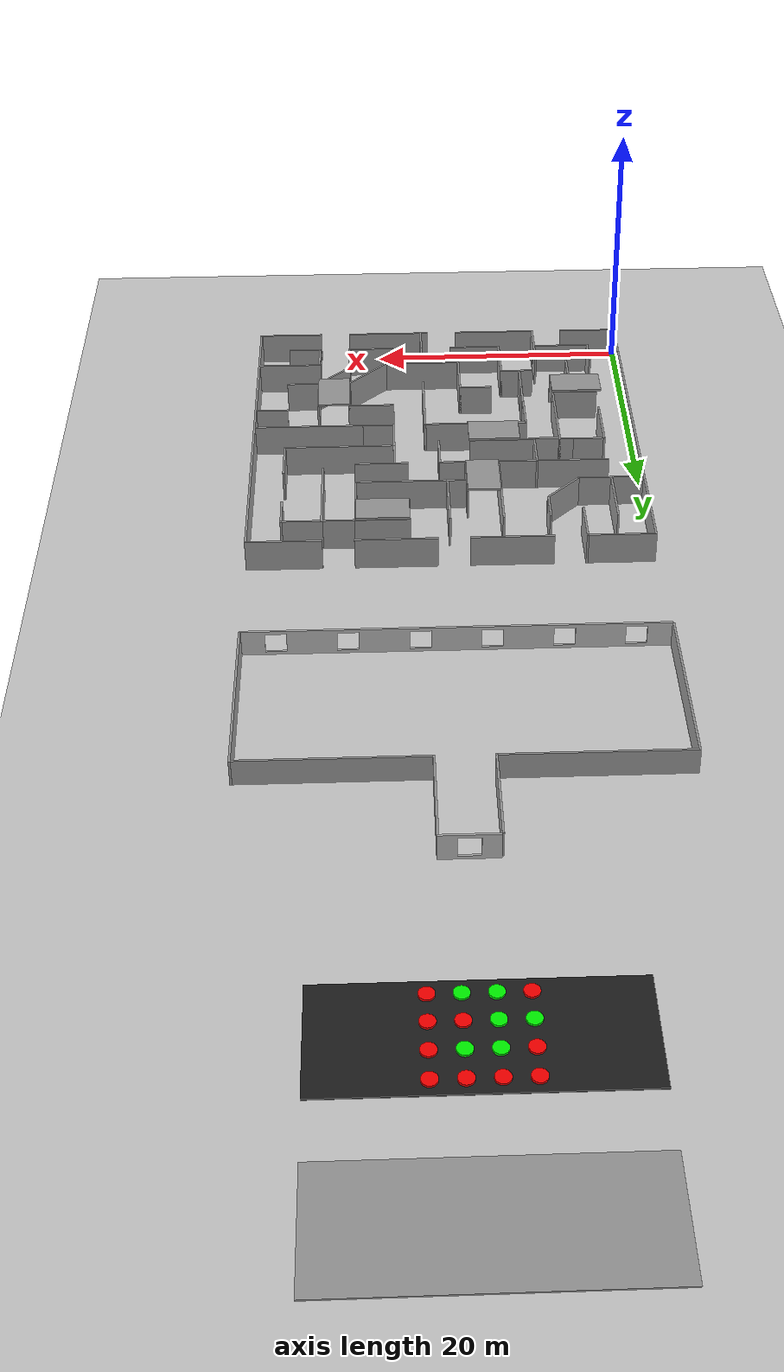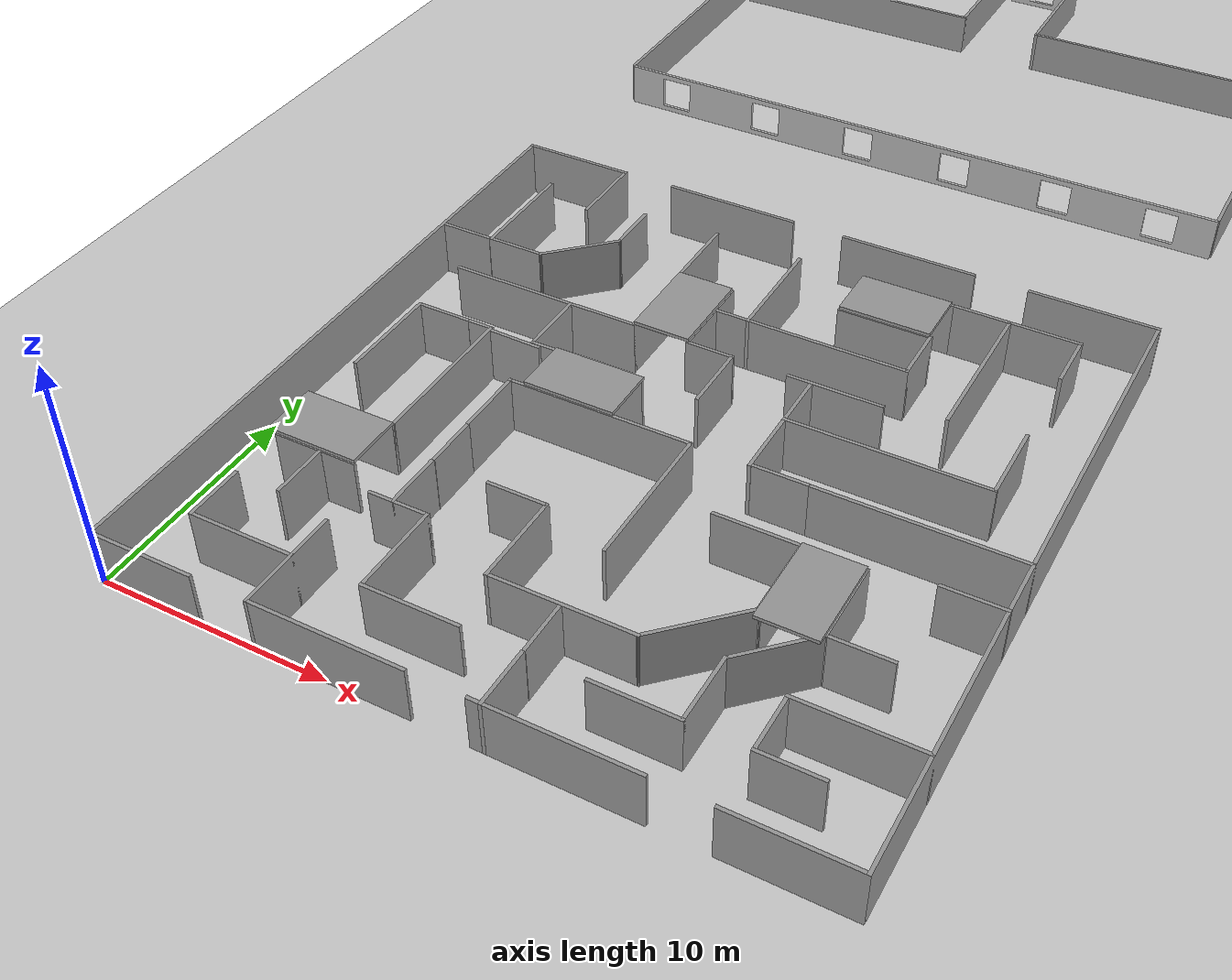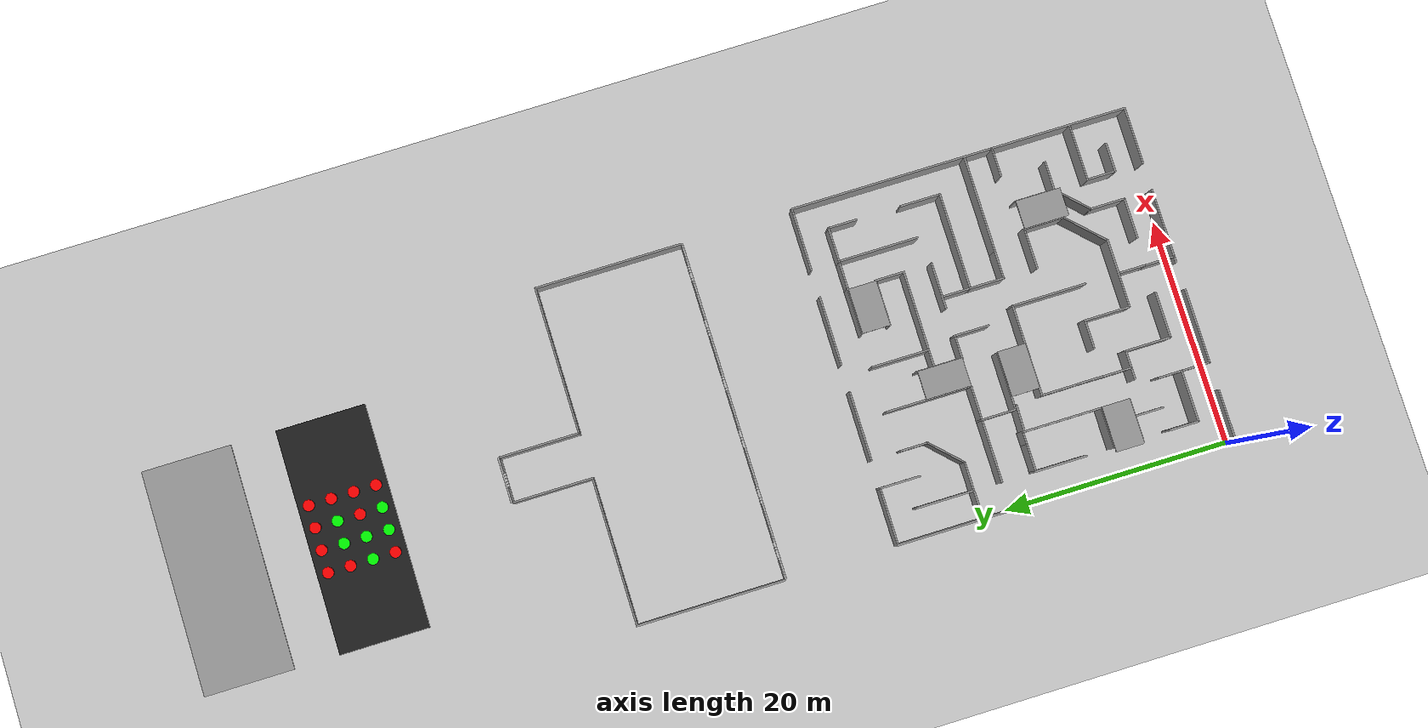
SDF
<sdf version="1.6">
 <world name="default">
  <light name="sun" type="directional">
   <pose>0 0 10 0 -0 0</pose>
   <diffuse>0.8 0.8 0.8 1</diffuse>
   <specular>0.2 0.2 0.2 1</specular>
   <attenuation>
    <range>1000</range>
    <constant>0.9</constant>
    <linear>0.01</linear>
    <quadratic>0.001</quadratic>
   </attenuation>
   <direction>-0.5 0.1 -0.9</direction>
  </light>
  <model name="ground_plane">
   <pose>15 45 0 0 -0 0</pose>
   <static>1</static>
   <link name="link">
    <collision name="collision">
     <geometry><plane><normal>0 0 1</normal><size>100 100</size></plane></geometry>
     <surface><friction><ode><mu>100</mu><mu2>50</mu2></ode></friction></surface>
    </collision>
    <visual name="visual">
     <cast_shadows>0</cast_shadows>
     <geometry><plane><normal>0 0 1</normal><size>30 120</size></plane></geometry>
     <material>
      <script><uri>file://media/materials/scripts/gazebo.material</uri><name>Gazebo/Grey</name></script>
     </material>
    </visual>
   </link>
  </model>
  <gravity>0 0 -9.8</gravity>
  <magnetic_field>6e-06 2.3e-05 -4.2e-05</magnetic_field>
  <atmosphere type="adiabatic"/>
  <physics name="default_physics" default="0" type="ode">
   <max_step_size>0.001</max_step_size>
   <real_time_factor>1</real_time_factor>
   <real_time_update_rate>1000</real_time_update_rate>
  </physics>
  <scene><ambient>0.4 0.4 0.4 1</ambient><background>0.7 0.7 0.7 1</background><shadows>1</shadows></scene>
  <spherical_coordinates>
   <surface_model>EARTH_WGS84</surface_model>
   <latitude_deg>0</latitude_deg>
   <longitude_deg>0</longitude_deg>
   <elevation>0</elevation>
   <heading_deg>0</heading_deg>
  </spherical_coordinates>
  <model name="platform">
   <link name="link_0">
    <inertial>
     <mass>1</mass>
     <inertia>
      <ixx>0.166667</ixx>
      <ixy>0</ixy>
      <ixz>0</ixz>
      <iyy>0.166667</iyy>
      <iyz>0</iyz>
      <izz>0.166667</izz>
     </inertia>
    </inertial>
    <visual name="visual">
     <geometry><box><size>20 8 0.1</size></box></geometry>
     <material>
      <lighting>1</lighting>
      <script><uri>file://media/materials/scripts/gazebo.material</uri><name>Gazebo/Black</name></script>
      <shader type="pixel"><normal_map>__default__</normal_map></shader>
      <ambient>0.3 0.3 0.3 1</ambient>
      <diffuse>0.7 0.7 0.7 1</diffuse>
      <specular>0.01 0.01 0.01 1</specular>
      <emissive>0 0 0 1</emissive>
     </material>
    </visual>
    <collision name="collision">
     <geometry><box><size>20 8 0.1</size></box></geometry>
     <surface>
      <friction>
       <ode><mu>1</mu><mu2>1</mu2><fdir1>0 0 0</fdir1><slip1>0</slip1><slip2>0</slip2></ode>
       <torsional>
        <coefficient>1</coefficient>
        <patch_radius>0</patch_radius>
        <surface_radius>0</surface_radius>
        <use_patch_radius>1</use_patch_radius>
        <ode><slip>0</slip></ode>
       </torsional>
      </friction>
      <bounce><restitution_coefficient>0</restitution_coefficient><threshold>1e+06</threshold></bounce>
      <contact>
       <collide_without_contact>0</collide_without_contact>
       <collide_without_contact_bitmask>1</collide_without_contact_bitmask>
       <collide_bitmask>1</collide_bitmask>
       <ode>
        <soft_cfm>0</soft_cfm>
        <soft_erp>0.2</soft_erp>
        <kp>1e+13</kp>
        <kd>1</kd>
        <max_vel>0.01</max_vel>
        <min_depth>0</min_depth>
       </ode>
       <bullet>
        <split_impulse>1</split_impulse>
        <split_impulse_penetration_threshold>-0.01</split_impulse_penetration_threshold>
        <soft_cfm>0</soft_cfm>
        <soft_erp>0.2</soft_erp>
        <kp>1e+13</kp>
        <kd>1</kd>
       </bullet>
      </contact>
     </surface>
    </collision>
   </link>
   <static>0</static>
   <pose>15.0041 73.9996 0.049979 -8e-06 1e-06 -0.000229</pose>
  </model>
  <model name="platform_0">
   <link name="link_0">
    <inertial>
     <mass>1</mass>
     <inertia>
      <ixx>0.166667</ixx>
      <ixy>0</ixy>
      <ixz>0</ixz>
      <iyy>0.166667</iyy>
      <iyz>0</iyz>
      <izz>0.166667</izz>
     </inertia>
    </inertial>
    <visual name="visual">
     <geometry><box><size>20 8 0.1</size></box></geometry>
     <material>
      <lighting>1</lighting>
      <script><uri>file://media/materials/scripts/gazebo.material</uri><name>Gazebo/Grey</name></script>
      <shader type="pixel"><normal_map>__default__</normal_map></shader>
      <ambient>0.3 0.3 0.3 1</ambient>
      <diffuse>0.7 0.7 0.7 1</diffuse>
      <specular>0.01 0.01 0.01 1</specular>
      <emissive>0 0 0 1</emissive>
     </material>
    </visual>
    <collision name="collision">
     <geometry><box><size>20 8 0.1</size></box></geometry>
     <surface>
      <friction>
       <ode><mu>1</mu><mu2>1</mu2><fdir1>0 0 0</fdir1><slip1>0</slip1><slip2>0</slip2></ode>
       <torsional>
        <coefficient>1</coefficient>
        <patch_radius>0</patch_radius>
        <surface_radius>0</surface_radius>
        <use_patch_radius>1</use_patch_radius>
        <ode><slip>0</slip></ode>
       </torsional>
      </friction>
      <bounce><restitution_coefficient>0</restitution_coefficient><threshold>1e+06</threshold></bounce>
      <contact>
       <collide_without_contact>0</collide_without_contact>
       <collide_without_contact_bitmask>1</collide_without_contact_bitmask>
       <collide_bitmask>1</collide_bitmask>
       <ode>
        <soft_cfm>0</soft_cfm>
        <soft_erp>0.2</soft_erp>
        <kp>1e+13</kp>
        <kd>1</kd>
        <max_vel>0.01</max_vel>
        <min_depth>0</min_depth>
       </ode>
       <bullet>
        <split_impulse>1</split_impulse>
        <split_impulse_penetration_threshold>-0.01</split_impulse_penetration_threshold>
        <soft_cfm>0</soft_cfm>
        <soft_erp>0.2</soft_erp>
        <kp>1e+13</kp>
        <kd>1</kd>
       </bullet>
      </contact>
     </surface>
    </collision>
   </link>
   <static>0</static>
   <pose>15.0041 85.9996 0.049979 -8e-06 1e-06 -0.000229</pose>
  </model>
  <model name="red">
   <static>1</static>
   <link name="link">
    <visual name="visual"><geometry><mesh><uri>model://red/meshes/red.dae</uri></mesh></geometry></visual>
   </link>
   <pose>12 71 0.15 0 -0 0</pose>
  </model>
  <model name="red_0">
   <static>1</static>
   <link name="link">
    <visual name="visual"><geometry><mesh><uri>model://red/meshes/red.dae</uri></mesh></geometry></visual>
   </link>
   <pose>12 75 0.15 0 -0 0</pose>
  </model>
  <model name="red_1">
   <static>1</static>
   <link name="link">
    <visual name="visual"><geometry><mesh><uri>model://red/meshes/red.dae</uri></mesh></geometry></visual>
   </link>
   <pose>12 77 0.15 0 -0 0</pose>
  </model>
  <model name="red_2">
   <static>1</static>
   <link name="link">
    <visual name="visual"><geometry><mesh><uri>model://red/meshes/red.dae</uri></mesh></geometry></visual>
   </link>
   <pose>14 77 0.15 0 -0 0</pose>
  </model>
  <model name="red_3">
   <static>1</static>
   <link name="link">
    <visual name="visual"><geometry><mesh><uri>model://red/meshes/red.dae</uri></mesh></geometry></visual>
   </link>
   <pose>16 73 0.15 0 -0 0</pose>
  </model>
  <model name="red_4">
   <static>1</static>
   <link name="link">
    <visual name="visual"><geometry><mesh><uri>model://red/meshes/red.dae</uri></mesh></geometry></visual>
   </link>
   <pose>16 77 0.15 0 -0 0</pose>
  </model>
  <model name="red_5">
   <static>1</static>
   <link name="link">
    <visual name="visual"><geometry><mesh><uri>model://red/meshes/red.dae</uri></mesh></geometry></visual>
   </link>
   <pose>18 71 0.15 0 -0 0</pose>
  </model>
  <model name="red_6">
   <static>1</static>
   <link name="link">
    <visual name="visual"><geometry><mesh><uri>model://red/meshes/red.dae</uri></mesh></geometry></visual>
   </link>
   <pose>18 73 0.15 0 -0 0</pose>
  </model>
  <model name="red_7">
   <static>1</static>
   <link name="link">
    <visual name="visual"><geometry><mesh><uri>model://red/meshes/red.dae</uri></mesh></geometry></visual>
   </link>
   <pose>18 75 0.15 0 -0 0</pose>
  </model>
  <model name="red_8">
   <static>1</static>
   <link name="link">
    <visual name="visual"><geometry><mesh><uri>model://red/meshes/red.dae</uri></mesh></geometry></visual>
   </link>
   <pose>18 77 0.15 0 -0 0</pose>
  </model>
  <model name="green">
   <static>1</static>
   <link name="link">
    <visual name="visual"><geometry><mesh><uri>model://green/meshes/green.dae</uri></mesh></geometry></visual>
   </link>
   <pose>12 73 0.15 0 -0 0</pose>
  </model>
  <model name="green_0">
   <static>1</static>
   <link name="link">
    <visual name="visual"><geometry><mesh><uri>model://green/meshes/green.dae</uri></mesh></geometry></visual>
   </link>
   <pose>14 71 0.15 0 -0 0</pose>
  </model>
  <model name="green_1">
   <static>1</static>
   <link name="link">
    <visual name="visual"><geometry><mesh><uri>model://green/meshes/green.dae</uri></mesh></geometry></visual>
   </link>
   <pose>14 73 0.15 0 -0 0</pose>
  </model>
  <model name="green_2">
   <static>1</static>
   <link name="link">
    <visual name="visual"><geometry><mesh><uri>model://green/meshes/green.dae</uri></mesh></geometry></visual>
   </link>
   <pose>14 75 0.15 0 -0 0</pose>
  </model>
  <model name="green_3">
   <static>1</static>
   <link name="link">
    <visual name="visual"><geometry><mesh><uri>model://green/meshes/green.dae</uri></mesh></geometry></visual>
   </link>
   <pose>16 71 0.15 0 -0 0</pose>
  </model>
  <model name="green_4">
   <static>1</static>
   <link name="link">
    <visual name="visual"><geometry><mesh><uri>model://green/meshes/green.dae</uri></mesh></geometry></visual>
   </link>
   <pose>16 75 0.15 0 -0 0</pose>
  </model>
  <model name="Untitled">
   <pose>15 15 0 0 -0 1.57</pose>
   <link name="Wall_101">
    <collision name="Wall_101_Collision">
     <geometry><box><size>2.65 0.15 2.5</size></box></geometry>
     <pose>0 0 1.25 0 -0 0</pose>
    </collision>
    <visual name="Wall_101_Visual">
     <pose>0 0 1.25 0 -0 0</pose>
     <geometry><box><size>2.65 0.15 2.5</size></box></geometry>
     <material>
      <script><uri>file://media/materials/scripts/gazebo.material</uri><name>Gazebo/Grey</name></script>
      <ambient>1 1 1 1</ambient>
     </material>
     <meta><layer>0</layer></meta>
    </visual>
    <pose>8.75 -7 0 0 -0 0</pose>
   </link>
   <link name="Wall_103">
    <collision name="Wall_103_Collision">
     <geometry><box><size>4.15 0.15 2.5</size></box></geometry>
     <pose>0 0 1.25 0 -0 0</pose>
    </collision>
    <visual name="Wall_103_Visual">
     <pose>0 0 1.25 0 -0 0</pose>
     <geometry><box><size>4.15 0.15 2.5</size></box></geometry>
     <material>
      <script><uri>file://media/materials/scripts/gazebo.material</uri><name>Gazebo/Grey</name></script>
      <ambient>1 1 1 1</ambient>
     </material>
     <meta><layer>0</layer></meta>
    </visual>
    <pose>10 -5 0 0 -0 1.5708</pose>
   </link>
   <link name="Wall_105">
    <collision name="Wall_105_Collision">
     <geometry><box><size>4.15 0.15 2.5</size></box></geometry>
     <pose>0 0 1.25 0 -0 0</pose>
    </collision>
    <visual name="Wall_105_Visual">
     <pose>0 0 1.25 0 -0 0</pose>
     <geometry><box><size>4.15 0.15 2.5</size></box></geometry>
     <material>
      <script><uri>file://media/materials/scripts/gazebo.material</uri><name>Gazebo/Grey</name></script>
      <ambient>1 1 1 1</ambient>
     </material>
     <meta><layer>0</layer></meta>
    </visual>
    <pose>12.5 -5 0 0 -0 -1.5708</pose>
   </link>
   <link name="Wall_107">
    <collision name="Wall_107_Collision">
     <geometry><box><size>7.15 0.15 2.5</size></box></geometry>
     <pose>0 0 1.25 0 -0 0</pose>
    </collision>
    <visual name="Wall_107_Visual">
     <pose>0 0 1.25 0 -0 0</pose>
     <geometry><box><size>7.15 0.15 2.5</size></box></geometry>
     <material>
      <script><uri>file://media/materials/scripts/gazebo.material</uri><name>Gazebo/Grey</name></script>
      <ambient>1 1 1 1</ambient>
     </material>
     <meta><layer>0</layer></meta>
    </visual>
    <pose>9 -9.5 0 0 -0 0</pose>
   </link>
   <link name="Wall_111">
    <collision name="Wall_111_Collision">
     <geometry><box><size>5.15 0.15 2.5</size></box></geometry>
     <pose>0 0 1.25 0 -0 0</pose>
    </collision>
    <visual name="Wall_111_Visual">
     <pose>0 0 1.25 0 -0 0</pose>
     <geometry><box><size>5.15 0.15 2.5</size></box></geometry>
     <material>
      <script><uri>file://media/materials/scripts/gazebo.material</uri><name>Gazebo/Grey</name></script>
      <ambient>1 1 1 1</ambient>
     </material>
     <meta><layer>0</layer></meta>
    </visual>
    <pose>10 0 0 0 -0 0</pose>
   </link>
   <link name="Wall_113">
    <collision name="Wall_113_Collision">
     <geometry><box><size>5.15 0.15 2.5</size></box></geometry>
     <pose>0 0 1.25 0 -0 0</pose>
    </collision>
    <visual name="Wall_113_Visual">
     <pose>0 0 1.25 0 -0 0</pose>
     <geometry><box><size>5.15 0.15 2.5</size></box></geometry>
     <material>
      <script><uri>file://media/materials/scripts/gazebo.material</uri><name>Gazebo/Grey</name></script>
      <ambient>1 1 1 1</ambient>
     </material>
     <meta><layer>0</layer></meta>
    </visual>
    <pose>10 12.5 0 0 -0 0</pose>
   </link>
   <link name="Wall_115">
    <collision name="Wall_115_Collision">
     <geometry><box><size>3.65 0.15 2.5</size></box></geometry>
     <pose>0 0 1.25 0 -0 0</pose>
    </collision>
    <visual name="Wall_115_Visual">
     <pose>0 0 1.25 0 -0 0</pose>
     <geometry><box><size>3.65 0.15 2.5</size></box></geometry>
     <material>
      <script><uri>file://media/materials/scripts/gazebo.material</uri><name>Gazebo/Grey</name></script>
      <ambient>1 1 1 1</ambient>
     </material>
     <meta><layer>0</layer></meta>
    </visual>
    <pose>13.25 10 0 0 -0 3.14159</pose>
   </link>
   <link name="Wall_117">
    <collision name="Wall_117_Collision">
     <geometry><box><size>2.65 0.15 2.5</size></box></geometry>
     <pose>0 0 1.25 0 -0 0</pose>
    </collision>
    <visual name="Wall_117_Visual">
     <pose>0 0 1.25 0 -0 0</pose>
     <geometry><box><size>2.65 0.15 2.5</size></box></geometry>
     <material>
      <script><uri>file://media/materials/scripts/gazebo.material</uri><name>Gazebo/Grey</name></script>
      <ambient>1 1 1 1</ambient>
     </material>
     <meta><layer>0</layer></meta>
    </visual>
    <pose>-13.75 -1.5 0 0 -0 0</pose>
   </link>
   <link name="Wall_119">
    <collision name="Wall_119_Collision">
     <geometry><box><size>6.15 0.15 2.5</size></box></geometry>
     <pose>0 0 1.25 0 -0 0</pose>
    </collision>
    <visual name="Wall_119_Visual">
     <pose>0 0 1.25 0 -0 0</pose>
     <geometry><box><size>6.15 0.15 2.5</size></box></geometry>
     <material>
      <script><uri>file://media/materials/scripts/gazebo.material</uri><name>Gazebo/Grey</name></script>
      <ambient>1 1 1 1</ambient>
     </material>
     <meta><layer>0</layer></meta>
    </visual>
    <pose>-10 -1.5 0 0 -0 -1.5708</pose>
   </link>
   <link name="Wall_121">
    <collision name="Wall_121_Collision">
     <geometry><box><size>4.15 0.15 2.5</size></box></geometry>
     <pose>0 0 1.25 0 -0 0</pose>
    </collision>
    <visual name="Wall_121_Visual">
     <pose>0 0 1.25 0 -0 0</pose>
     <geometry><box><size>4.15 0.15 2.5</size></box></geometry>
     <material>
      <script><uri>file://media/materials/scripts/gazebo.material</uri><name>Gazebo/Grey</name></script>
      <ambient>1 1 1 1</ambient>
     </material>
     <meta><layer>0</layer></meta>
    </visual>
    <pose>-8 1.5 0 0 -0 0</pose>
   </link>
   <link name="Wall_123">
    <collision name="Wall_123_Collision">
     <geometry><box><size>2.65 0.15 2.5</size></box></geometry>
     <pose>0 0 1.25 0 -0 0</pose>
    </collision>
    <visual name="Wall_123_Visual">
     <pose>0 0 1.25 0 -0 0</pose>
     <geometry><box><size>2.65 0.15 2.5</size></box></geometry>
     <material>
      <script><uri>file://media/materials/scripts/gazebo.material</uri><name>Gazebo/Grey</name></script>
      <ambient>1 1 1 1</ambient>
     </material>
     <meta><layer>0</layer></meta>
    </visual>
    <pose>-6 2.75 0 0 -0 1.5708</pose>
   </link>
   <link name="Wall_125">
    <collision name="Wall_125_Collision">
     <geometry><box><size>4.39264 0.15 2.5</size></box></geometry>
     <pose>0 0 1.25 0 -0 0</pose>
    </collision>
    <visual name="Wall_125_Visual">
     <pose>0 0 1.25 0 -0 0</pose>
     <geometry><box><size>4.39264 0.15 2.5</size></box></geometry>
     <material>
      <script><uri>file://media/materials/scripts/gazebo.material</uri><name>Gazebo/Grey</name></script>
      <ambient>1 1 1 1</ambient>
     </material>
     <meta><layer>0</layer></meta>
    </visual>
    <pose>-8.5 -6 0 0 -0 -0.785398</pose>
   </link>
   <link name="Wall_127">
    <collision name="Wall_127_Collision">
     <geometry><box><size>3.65 0.15 2.5</size></box></geometry>
     <pose>0 0 1.25 0 -0 0</pose>
    </collision>
    <visual name="Wall_127_Visual">
     <pose>0 0 1.25 0 -0 0</pose>
     <geometry><box><size>3.65 0.15 2.5</size></box></geometry>
     <material>
      <script><uri>file://media/materials/scripts/gazebo.material</uri><name>Gazebo/Grey</name></script>
      <ambient>1 1 1 1</ambient>
     </material>
     <meta><layer>0</layer></meta>
    </visual>
    <pose>-5.25 -7.5 0 0 -0 0</pose>
   </link>
   <link name="Wall_128">
    <collision name="Wall_128_Collision">
     <geometry><box><size>3.65 0.15 2.5</size></box></geometry>
     <pose>0 0 1.25 0 -0 0</pose>
    </collision>
    <visual name="Wall_128_Visual">
     <pose>0 0 1.25 0 -0 0</pose>
     <geometry><box><size>3.65 0.15 2.5</size></box></geometry>
     <material>
      <script><uri>file://media/materials/scripts/gazebo.material</uri><name>Gazebo/Grey</name></script>
      <ambient>1 1 1 1</ambient>
     </material>
     <meta><layer>0</layer></meta>
    </visual>
    <pose>-3.5 -5.75 0 0 -0 1.5708</pose>
   </link>
   <link name="Wall_132">
    <collision name="Wall_132_Collision">
     <geometry><box><size>3.65 0.15 2.5</size></box></geometry>
     <pose>0 0 1.25 0 -0 0</pose>
    </collision>
    <visual name="Wall_132_Visual">
     <pose>0 0 1.25 0 -0 0</pose>
     <geometry><box><size>3.65 0.15 2.5</size></box></geometry>
     <material>
      <script><uri>file://media/materials/scripts/gazebo.material</uri><name>Gazebo/Grey</name></script>
      <ambient>1 1 1 1</ambient>
     </material>
     <meta><layer>0</layer></meta>
    </visual>
    <pose>-12.5 -5.75 0 0 -0 -1.5708</pose>
   </link>
   <link name="Wall_134">
    <collision name="Wall_134_Collision">
     <geometry><box><size>3.15 0.15 2.5</size></box></geometry>
     <pose>0 0 1.25 0 -0 0</pose>
    </collision>
    <visual name="Wall_134_Visual">
     <pose>0 0 1.25 0 -0 0</pose>
     <geometry><box><size>3.15 0.15 2.5</size></box></geometry>
     <material>
      <script><uri>file://media/materials/scripts/gazebo.material</uri><name>Gazebo/Grey</name></script>
      <ambient>1 1 1 1</ambient>
     </material>
     <meta><layer>0</layer></meta>
    </visual>
    <pose>-11 -7.5 0 0 -0 0</pose>
   </link>
   <link name="Wall_135">
    <collision name="Wall_135_Collision">
     <geometry><box><size>3.68553 0.15 2.5</size></box></geometry>
     <pose>0 0 1.25 0 -0 0</pose>
    </collision>
    <visual name="Wall_135_Visual">
     <pose>0 0 1.25 0 -0 0</pose>
     <geometry><box><size>3.68553 0.15 2.5</size></box></geometry>
     <material>
      <script><uri>file://media/materials/scripts/gazebo.material</uri><name>Gazebo/Grey</name></script>
      <ambient>1 1 1 1</ambient>
     </material>
     <meta><layer>0</layer></meta>
    </visual>
    <pose>-8.25 -8.75 0 0 -0 -0.785398</pose>
   </link>
   <link name="Wall_136">
    <collision name="Wall_136_Collision">
     <geometry><box><size>3.65 0.15 2.5</size></box></geometry>
     <pose>0 0 1.25 0 -0 0</pose>
    </collision>
    <visual name="Wall_136_Visual">
     <pose>0 0 1.25 0 -0 0</pose>
     <geometry><box><size>3.65 0.15 2.5</size></box></geometry>
     <material>
      <script><uri>file://media/materials/scripts/gazebo.material</uri><name>Gazebo/Grey</name></script>
      <ambient>1 1 1 1</ambient>
     </material>
     <meta><layer>0</layer></meta>
    </visual>
    <pose>-5.25 -10 0 0 -0 0</pose>
   </link>
   <link name="Wall_138">
    <collision name="Wall_138_Collision">
     <geometry><box><size>2.65 0.15 2.5</size></box></geometry>
     <pose>0 0 1.25 0 -0 0</pose>
    </collision>
    <visual name="Wall_138_Visual">
     <pose>0 0 1.25 0 -0 0</pose>
     <geometry><box><size>2.65 0.15 2.5</size></box></geometry>
     <material>
      <script><uri>file://media/materials/scripts/gazebo.material</uri><name>Gazebo/Grey</name></script>
      <ambient>1 1 1 1</ambient>
     </material>
     <meta><layer>0</layer></meta>
    </visual>
    <pose>-7 -11.25 0 0 -0 -1.5708</pose>
   </link>
   <link name="Wall_140">
    <collision name="Wall_140_Collision">
     <geometry><box><size>2.65 0.15 2.5</size></box></geometry>
     <pose>0 0 1.25 0 -0 0</pose>
    </collision>
    <visual name="Wall_140_Visual">
     <pose>0 0 1.25 0 -0 0</pose>
     <geometry><box><size>2.65 0.15 2.5</size></box></geometry>
     <material>
      <script><uri>file://media/materials/scripts/gazebo.material</uri><name>Gazebo/Grey</name></script>
      <ambient>1 1 1 1</ambient>
     </material>
     <meta><layer>0</layer></meta>
    </visual>
    <pose>-12.5 -11.25 0 0 -0 1.5708</pose>
   </link>
   <link name="Wall_142">
    <collision name="Wall_142_Collision">
     <geometry><box><size>5.15 0.15 2.5</size></box></geometry>
     <pose>0 0 1.25 0 -0 0</pose>
    </collision>
    <visual name="Wall_142_Visual">
     <pose>0 0 1.25 0 -0 0</pose>
     <geometry><box><size>5.15 0.15 2.5</size></box></geometry>
     <material>
      <script><uri>file://media/materials/scripts/gazebo.material</uri><name>Gazebo/Grey</name></script>
      <ambient>1 1 1 1</ambient>
     </material>
     <meta><layer>0</layer></meta>
    </visual>
    <pose>-10 -12.5 0 0 -0 -1.5708</pose>
   </link>
   <link name="Wall_144">
    <collision name="Wall_144_Collision">
     <geometry><box><size>2.65 0.15 2.5</size></box></geometry>
     <pose>0 0 1.25 0 -0 0</pose>
    </collision>
    <visual name="Wall_144_Visual">
     <pose>0 0 1.25 0 -0 0</pose>
     <geometry><box><size>2.65 0.15 2.5</size></box></geometry>
     <material>
      <script><uri>file://media/materials/scripts/gazebo.material</uri><name>Gazebo/Grey</name></script>
      <ambient>1 1 1 1</ambient>
     </material>
     <meta><layer>0</layer></meta>
    </visual>
    <pose>-3 -13.75 0 0 -0 1.5708</pose>
   </link>
   <link name="Wall_146">
    <collision name="Wall_146_Collision">
     <geometry><box><size>3.15 0.15 2.5</size></box></geometry>
     <pose>0 0 1.25 0 -0 0</pose>
    </collision>
    <visual name="Wall_146_Visual">
     <pose>0 0 1.25 0 -0 0</pose>
     <geometry><box><size>3.15 0.15 2.5</size></box></geometry>
     <material>
      <script><uri>file://media/materials/scripts/gazebo.material</uri><name>Gazebo/Grey</name></script>
      <ambient>1 1 1 1</ambient>
     </material>
     <meta><layer>0</layer></meta>
    </visual>
    <pose>1 -4 0 0 -0 0</pose>
   </link>
   <link name="Wall_148">
    <collision name="Wall_148_Collision">
     <geometry><box><size>4.15 0.15 2.5</size></box></geometry>
     <pose>0 0 1.25 0 -0 0</pose>
    </collision>
    <visual name="Wall_148_Visual">
     <pose>0 0 1.25 0 -0 0</pose>
     <geometry><box><size>4.15 0.15 2.5</size></box></geometry>
     <material>
      <script><uri>file://media/materials/scripts/gazebo.material</uri><name>Gazebo/Grey</name></script>
      <ambient>1 1 1 1</ambient>
     </material>
     <meta><layer>0</layer></meta>
    </visual>
    <pose>5 -5 0 0 -0 -1.5708</pose>
   </link>
   <link name="Wall_150">
    <collision name="Wall_150_Collision">
     <geometry><box><size>8.65 0.15 2.5</size></box></geometry>
     <pose>0 0 1.25 0 -0 0</pose>
    </collision>
    <visual name="Wall_150_Visual">
     <pose>0 0 1.25 0 -0 0</pose>
     <geometry><box><size>8.65 0.15 2.5</size></box></geometry>
     <material>
      <script><uri>file://media/materials/scripts/gazebo.material</uri><name>Gazebo/Grey</name></script>
      <ambient>1 1 1 1</ambient>
     </material>
     <meta><layer>0</layer></meta>
    </visual>
    <pose>2.5 -8.25 0 0 -0 -1.5708</pose>
   </link>
   <link name="Wall_151">
    <collision name="Wall_151_Collision">
     <geometry><box><size>3.65 0.15 2.5</size></box></geometry>
     <pose>0 0 1.25 0 -0 0</pose>
    </collision>
    <visual name="Wall_151_Visual">
     <pose>0 0 1.25 0 -0 0</pose>
     <geometry><box><size>3.65 0.15 2.5</size></box></geometry>
     <material>
      <script><uri>file://media/materials/scripts/gazebo.material</uri><name>Gazebo/Grey</name></script>
      <ambient>1 1 1 1</ambient>
     </material>
     <meta><layer>0</layer></meta>
    </visual>
    <pose>4.25 -12.5 0 0 -0 0</pose>
   </link>
   <link name="Wall_153">
    <collision name="Wall_153_Collision">
     <geometry><box><size>3.65 0.15 2.5</size></box></geometry>
     <pose>0 0 1.25 0 -0 0</pose>
    </collision>
    <visual name="Wall_153_Visual">
     <pose>0 0 1.25 0 -0 0</pose>
     <geometry><box><size>3.65 0.15 2.5</size></box></geometry>
     <material>
      <script><uri>file://media/materials/scripts/gazebo.material</uri><name>Gazebo/Grey</name></script>
      <ambient>1 1 1 1</ambient>
     </material>
     <meta><layer>0</layer></meta>
    </visual>
    <pose>-7.5 10.75 0 0 -0 -1.5708</pose>
   </link>
   <link name="Wall_155">
    <collision name="Wall_155_Collision">
     <geometry><box><size>3.65 0.15 2.5</size></box></geometry>
     <pose>0 0 1.25 0 -0 0</pose>
    </collision>
    <visual name="Wall_155_Visual">
     <pose>0 0 1.25 0 -0 0</pose>
     <geometry><box><size>3.65 0.15 2.5</size></box></geometry>
     <material>
      <script><uri>file://media/materials/scripts/gazebo.material</uri><name>Gazebo/Grey</name></script>
      <ambient>1 1 1 1</ambient>
     </material>
     <meta><layer>0</layer></meta>
    </visual>
    <pose>-5 10.75 0 0 -0 -1.5708</pose>
   </link>
   <link name="Wall_157">
    <collision name="Wall_157_Collision">
     <geometry><box><size>2.65 0.15 2.5</size></box></geometry>
     <pose>0 0 1.25 0 -0 0</pose>
    </collision>
    <visual name="Wall_157_Visual">
     <pose>0 0 1.25 0 -0 0</pose>
     <geometry><box><size>2.65 0.15 2.5</size></box></geometry>
     <material>
      <script><uri>file://media/materials/scripts/gazebo.material</uri><name>Gazebo/Grey</name></script>
      <ambient>1 1 1 1</ambient>
     </material>
     <meta><layer>0</layer></meta>
    </visual>
    <pose>-7.25 6.5 0 0 -0 0</pose>
   </link>
   <link name="Wall_159">
    <collision name="Wall_159_Collision">
     <geometry><box><size>3.15 0.15 2.5</size></box></geometry>
     <pose>0 0 1.25 0 -0 0</pose>
    </collision>
    <visual name="Wall_159_Visual">
     <pose>0 0 1.25 0 -0 0</pose>
     <geometry><box><size>3.15 0.15 2.5</size></box></geometry>
     <material>
      <script><uri>file://media/materials/scripts/gazebo.material</uri><name>Gazebo/Grey</name></script>
      <ambient>1 1 1 1</ambient>
     </material>
     <meta><layer>0</layer></meta>
    </visual>
    <pose>-2 6.5 0 0 -0 3.14159</pose>
   </link>
   <link name="Wall_161">
    <collision name="Wall_161_Collision">
     <geometry><box><size>7.15 0.15 2.5</size></box></geometry>
     <pose>0 0 1.25 0 -0 0</pose>
    </collision>
    <visual name="Wall_161_Visual">
     <pose>0 0 1.25 0 -0 0</pose>
     <geometry><box><size>7.15 0.15 2.5</size></box></geometry>
     <material>
      <script><uri>file://media/materials/scripts/gazebo.material</uri><name>Gazebo/Grey</name></script>
      <ambient>1 1 1 1</ambient>
     </material>
     <meta><layer>0</layer></meta>
    </visual>
    <pose>-1.5 9 0 0 -0 0</pose>
   </link>
   <link name="Wall_163">
    <collision name="Wall_163_Collision">
     <geometry><box><size>1.15 0.15 2.5</size></box></geometry>
     <pose>0 0 1.25 0 -0 0</pose>
    </collision>
    <visual name="Wall_163_Visual">
     <pose>0 0 1.25 0 -0 0</pose>
     <geometry><box><size>1.15 0.15 2.5</size></box></geometry>
     <material>
      <script><uri>file://media/materials/scripts/gazebo.material</uri><name>Gazebo/Grey</name></script>
      <ambient>1 1 1 1</ambient>
     </material>
     <meta><layer>0</layer></meta>
    </visual>
    <pose>2 9.5 0 0 -0 1.5708</pose>
   </link>
   <link name="Wall_165">
    <collision name="Wall_165_Collision">
     <geometry><box><size>5.15 0.15 2.5</size></box></geometry>
     <pose>0 0 1.25 0 -0 0</pose>
    </collision>
    <visual name="Wall_165_Visual">
     <pose>0 0 1.25 0 -0 0</pose>
     <geometry><box><size>5.15 0.15 2.5</size></box></geometry>
     <material>
      <script><uri>file://media/materials/scripts/gazebo.material</uri><name>Gazebo/Grey</name></script>
      <ambient>1 1 1 1</ambient>
     </material>
     <meta><layer>0</layer></meta>
    </visual>
    <pose>2 4.5 0 0 -0 -1.5708</pose>
   </link>
   <link name="Wall_167">
    <collision name="Wall_167_Collision">
     <geometry><box><size>2.65 0.15 2.5</size></box></geometry>
     <pose>0 0 1.25 0 -0 0</pose>
    </collision>
    <visual name="Wall_167_Visual">
     <pose>0 0 1.25 0 -0 0</pose>
     <geometry><box><size>2.65 0.15 2.5</size></box></geometry>
     <material>
      <script><uri>file://media/materials/scripts/gazebo.material</uri><name>Gazebo/Grey</name></script>
      <ambient>1 1 1 1</ambient>
     </material>
     <meta><layer>0</layer></meta>
    </visual>
    <pose>7.5 11.25 0 0 -0 1.5708</pose>
   </link>
   <link name="Wall_169">
    <collision name="Wall_169_Collision">
     <geometry><box><size>8.65 0.15 2.5</size></box></geometry>
     <pose>0 0 1.25 0 -0 0</pose>
    </collision>
    <visual name="Wall_169_Visual">
     <pose>0 0 1.25 0 -0 0</pose>
     <geometry><box><size>8.65 0.15 2.5</size></box></geometry>
     <material>
      <script><uri>file://media/materials/scripts/gazebo.material</uri><name>Gazebo/Grey</name></script>
      <ambient>1 1 1 1</ambient>
     </material>
     <meta><layer>0</layer></meta>
    </visual>
    <pose>-0.5 -10.75 0 0 -0 -1.5708</pose>
   </link>
   <link name="Wall_171">
    <collision name="Wall_171_Collision">
     <geometry><box><size>3.15 0.15 2.5</size></box></geometry>
     <pose>0 0 1.25 0 -0 0</pose>
    </collision>
    <visual name="Wall_171_Visual">
     <pose>0 0 1.25 0 -0 0</pose>
     <geometry><box><size>3.15 0.15 2.5</size></box></geometry>
     <material>
      <script><uri>file://media/materials/scripts/gazebo.material</uri><name>Gazebo/Grey</name></script>
      <ambient>1 1 1 1</ambient>
     </material>
     <meta><layer>0</layer></meta>
    </visual>
    <pose>12.5 -11 0 0 -0 -1.5708</pose>
   </link>
   <link name="Wall_172">
    <collision name="Wall_172_Collision">
     <geometry><box><size>2.65 0.15 2.5</size></box></geometry>
     <pose>0 0 1.25 0 -0 0</pose>
    </collision>
    <visual name="Wall_172_Visual">
     <pose>0 0 1.25 0 -0 0</pose>
     <geometry><box><size>2.65 0.15 2.5</size></box></geometry>
     <material>
      <script><uri>file://media/materials/scripts/gazebo.material</uri><name>Gazebo/Grey</name></script>
      <ambient>1 1 1 1</ambient>
     </material>
     <meta><layer>0</layer></meta>
    </visual>
    <pose>11.25 -12.5 0 0 -0 3.14159</pose>
   </link>
   <link name="Wall_31">
    <collision name="Wall_31_Collision">
     <geometry><box><size>30.15 0.15 2.5</size></box></geometry>
     <pose>0 0 1.25 0 -0 0</pose>
    </collision>
    <visual name="Wall_31_Visual">
     <pose>0 0 1.25 0 -0 0</pose>
     <geometry><box><size>30.15 0.15 2.5</size></box></geometry>
     <material>
      <script><uri>file://media/materials/scripts/gazebo.material</uri><name>Gazebo/Grey</name></script>
      <ambient>1 1 1 1</ambient>
     </material>
     <meta><layer>0</layer></meta>
    </visual>
    <pose>-0 15 0 0 -0 0</pose>
   </link>
   <link name="Wall_35">
    <collision name="Wall_35_Collision">
     <geometry><box><size>30.15 0.15 2.5</size></box></geometry>
     <pose>0 0 1.25 0 -0 0</pose>
    </collision>
    <visual name="Wall_35_Visual">
     <pose>0 0 1.25 0 -0 0</pose>
     <geometry><box><size>30.15 0.15 2.5</size></box></geometry>
     <material>
      <script><uri>file://media/materials/scripts/gazebo.material</uri><name>Gazebo/Grey</name></script>
      <ambient>1 1 1 1</ambient>
     </material>
     <meta><layer>0</layer></meta>
    </visual>
    <pose>-0 -15 0 0 -0 0</pose>
   </link>
   <link name="Wall_37">
    <collision name="Wall_37_Collision">
     <geometry><box><size>4.65 0.15 2.5</size></box></geometry>
     <pose>0 0 1.25 0 -0 0</pose>
    </collision>
    <visual name="Wall_37_Visual">
     <pose>0 0 1.25 0 -0 0</pose>
     <geometry><box><size>4.65 0.15 2.5</size></box></geometry>
     <material>
      <script><uri>file://media/materials/scripts/gazebo.material</uri><name>Gazebo/Grey</name></script>
      <ambient>1 1 1 1</ambient>
     </material>
     <meta><layer>0</layer></meta>
    </visual>
    <pose>-12.75 8 0 0 -0 0</pose>
   </link>
   <link name="Wall_39">
    <collision name="Wall_39_Collision">
     <geometry><box><size>4.65 0.15 2.5</size></box></geometry>
     <pose>0 0 1.25 0 -0 0</pose>
    </collision>
    <visual name="Wall_39_Visual">
     <pose>0 0 1.25 0 -0 0</pose>
     <geometry><box><size>4.65 0.15 2.5</size></box></geometry>
     <material>
      <script><uri>file://media/materials/scripts/gazebo.material</uri><name>Gazebo/Grey</name></script>
      <ambient>1 1 1 1</ambient>
     </material>
     <meta><layer>0</layer></meta>
    </visual>
    <pose>-12.5 10.25 0 0 -0 1.5708</pose>
   </link>
   <link name="Wall_41">
    <collision name="Wall_41_Collision">
     <geometry><box><size>2.65 0.15 2.5</size></box></geometry>
     <pose>0 0 1.25 0 -0 0</pose>
    </collision>
    <visual name="Wall_41_Visual">
     <pose>0 0 1.25 0 -0 0</pose>
     <geometry><box><size>2.65 0.15 2.5</size></box></geometry>
     <material>
      <script><uri>file://media/materials/scripts/gazebo.material</uri><name>Gazebo/Grey</name></script>
      <ambient>1 1 1 1</ambient>
     </material>
     <meta><layer>0</layer></meta>
    </visual>
    <pose>-11.25 12.5 0 0 -0 0</pose>
   </link>
   <link name="Wall_43">
    <collision name="Wall_43_Collision">
     <geometry><box><size>2.65 0.15 2.5</size></box></geometry>
     <pose>0 0 1.25 0 -0 0</pose>
    </collision>
    <visual name="Wall_43_Visual">
     <pose>0 0 1.25 0 -0 0</pose>
     <geometry><box><size>2.65 0.15 2.5</size></box></geometry>
     <material>
      <script><uri>file://media/materials/scripts/gazebo.material</uri><name>Gazebo/Grey</name></script>
      <ambient>1 1 1 1</ambient>
     </material>
     <meta><layer>0</layer></meta>
    </visual>
    <pose>-8.75 10.5 0 0 -0 0</pose>
   </link>
   <link name="Wall_49">
    <collision name="Wall_49_Collision">
     <geometry><box><size>4.65 0.15 2.5</size></box></geometry>
     <pose>0 0 1.25 0 -0 0</pose>
    </collision>
    <visual name="Wall_49_Visual">
     <pose>0 0 1.25 0 -0 0</pose>
     <geometry><box><size>4.65 0.15 2.5</size></box></geometry>
     <material>
      <script><uri>file://media/materials/scripts/gazebo.material</uri><name>Gazebo/Grey</name></script>
      <ambient>1 1 1 1</ambient>
     </material>
     <meta><layer>0</layer></meta>
    </visual>
    <pose>-0.25 12.5 0 0 -0 3.14159</pose>
   </link>
   <link name="Wall_53">
    <collision name="Wall_53_Collision">
     <geometry><box><size>3.15 0.15 2.5</size></box></geometry>
     <pose>0 0 1.25 0 -0 0</pose>
    </collision>
    <visual name="Wall_53_Visual">
     <pose>0 0 1.25 0 -0 0</pose>
     <geometry><box><size>3.15 0.15 2.5</size></box></geometry>
     <material>
      <script><uri>file://media/materials/scripts/gazebo.material</uri><name>Gazebo/Grey</name></script>
      <ambient>1 1 1 1</ambient>
     </material>
     <meta><layer>0</layer></meta>
    </visual>
    <pose>3.5 7 0 0 -0 0</pose>
   </link>
   <link name="Wall_55">
    <collision name="Wall_55_Collision">
     <geometry><box><size>8.65 0.15 2.5</size></box></geometry>
     <pose>0 0 1.25 0 -0 0</pose>
    </collision>
    <visual name="Wall_55_Visual">
     <pose>0 0 1.25 0 -0 0</pose>
     <geometry><box><size>8.65 0.15 2.5</size></box></geometry>
     <material>
      <script><uri>file://media/materials/scripts/gazebo.material</uri><name>Gazebo/Grey</name></script>
      <ambient>1 1 1 1</ambient>
     </material>
     <meta><layer>0</layer></meta>
    </visual>
    <pose>5 8.25 0 0 -0 -1.5708</pose>
   </link>
   <link name="Wall_57">
    <collision name="Wall_57_Collision">
     <geometry><box><size>7.65 0.15 2.5</size></box></geometry>
     <pose>0 0 1.25 0 -0 0</pose>
    </collision>
    <visual name="Wall_57_Visual">
     <pose>0 0 1.25 0 -0 0</pose>
     <geometry><box><size>7.65 0.15 2.5</size></box></geometry>
     <material>
      <script><uri>file://media/materials/scripts/gazebo.material</uri><name>Gazebo/Grey</name></script>
      <ambient>1 1 1 1</ambient>
     </material>
     <meta><layer>0</layer></meta>
    </visual>
    <pose>8.75 4 0 0 -0 0</pose>
   </link>
   <link name="Wall_61">
    <collision name="Wall_61_Collision">
     <geometry><box><size>3.68553 0.15 2.5</size></box></geometry>
     <pose>0 0 1.25 0 -0 0</pose>
    </collision>
    <visual name="Wall_61_Visual">
     <pose>0 0 1.25 0 -0 0</pose>
     <geometry><box><size>3.68553 0.15 2.5</size></box></geometry>
     <material>
      <script><uri>file://media/materials/scripts/gazebo.material</uri><name>Gazebo/Grey</name></script>
      <ambient>1 1 1 1</ambient>
     </material>
     <meta><layer>0</layer></meta>
    </visual>
    <pose>8.75 8.75 0 0 -0 -0.785398</pose>
   </link>
   <link name="Wall_63">
    <collision name="Wall_63_Collision">
     <geometry><box><size>2.5 0.15 2.5</size></box></geometry>
     <pose>0 0 1.25 0 -0 0</pose>
    </collision>
    <visual name="Wall_63_Visual">
     <pose>0 0 1.25 0 -0 0</pose>
     <geometry><box><size>2.5 0.15 2.5</size></box></geometry>
     <material>
      <script><uri>file://media/materials/scripts/gazebo.material</uri><name>Gazebo/Grey</name></script>
      <ambient>1 1 1 1</ambient>
     </material>
     <meta><layer>0</layer></meta>
    </visual>
    <pose>11.175 7.5 0 0 -0 0</pose>
   </link>
   <link name="Wall_65">
    <collision name="Wall_65_Collision">
     <geometry><box><size>5.15 0.15 2.5</size></box></geometry>
     <pose>0 0 1.25 0 -0 0</pose>
    </collision>
    <visual name="Wall_65_Visual">
     <pose>0 0 1.25 0 -0 0</pose>
     <geometry><box><size>5.15 0.15 2.5</size></box></geometry>
     <material>
      <script><uri>file://media/materials/scripts/gazebo.material</uri><name>Gazebo/Grey</name></script>
      <ambient>1 1 1 1</ambient>
     </material>
     <meta><layer>0</layer></meta>
    </visual>
    <pose>15 12.5 0 0 -0 -1.5708</pose>
   </link>
   <link name="Wall_67">
    <collision name="Wall_67_Collision">
     <geometry><box><size>6.15 0.15 2.5</size></box></geometry>
     <pose>0 0 1.25 0 -0 0</pose>
    </collision>
    <visual name="Wall_67_Visual">
     <pose>0 0 1.25 0 -0 0</pose>
     <geometry><box><size>6.15 0.15 2.5</size></box></geometry>
     <material>
      <script><uri>file://media/materials/scripts/gazebo.material</uri><name>Gazebo/Grey</name></script>
      <ambient>1 1 1 1</ambient>
     </material>
     <meta><layer>0</layer></meta>
    </visual>
    <pose>15 4.5 0 0 -0 -1.5708</pose>
   </link>
   <link name="Wall_69">
    <collision name="Wall_69_Collision">
     <geometry><box><size>6.15 0.15 2.5</size></box></geometry>
     <pose>0 0 1.25 0 -0 0</pose>
    </collision>
    <visual name="Wall_69_Visual">
     <pose>0 0 1.25 0 -0 0</pose>
     <geometry><box><size>6.15 0.15 2.5</size></box></geometry>
     <material>
      <script><uri>file://media/materials/scripts/gazebo.material</uri><name>Gazebo/Grey</name></script>
      <ambient>1 1 1 1</ambient>
     </material>
     <meta><layer>0</layer></meta>
    </visual>
    <pose>15 -4 0 0 -0 -1.5708</pose>
   </link>
   <link name="Wall_71">
    <collision name="Wall_71_Collision">
     <geometry><box><size>5.65 0.15 2.5</size></box></geometry>
     <pose>0 0 1.25 0 -0 0</pose>
    </collision>
    <visual name="Wall_71_Visual">
     <pose>0 0 1.25 0 -0 0</pose>
     <geometry><box><size>5.65 0.15 2.5</size></box></geometry>
     <material>
      <script><uri>file://media/materials/scripts/gazebo.material</uri><name>Gazebo/Grey</name></script>
      <ambient>1 1 1 1</ambient>
     </material>
     <meta><layer>0</layer></meta>
    </visual>
    <pose>15 -12.25 0 0 -0 1.5708</pose>
   </link>
   <link name="Wall_73">
    <collision name="Wall_73_Collision">
     <geometry><box><size>4.65 0.15 2.5</size></box></geometry>
     <pose>0 0 1.25 0 -0 0</pose>
    </collision>
    <visual name="Wall_73_Visual">
     <pose>0 0 1.25 0 -0 0</pose>
     <geometry><box><size>4.65 0.15 2.5</size></box></geometry>
     <material>
      <script><uri>file://media/materials/scripts/gazebo.material</uri><name>Gazebo/Grey</name></script>
      <ambient>1 1 1 1</ambient>
     </material>
     <meta><layer>0</layer></meta>
    </visual>
    <pose>-15 12.75 0 0 -0 -1.5708</pose>
   </link>
   <link name="Wall_75">
    <collision name="Wall_75_Collision">
     <geometry><box><size>6.65 0.15 2.5</size></box></geometry>
     <pose>0 0 1.25 0 -0 0</pose>
    </collision>
    <visual name="Wall_75_Visual">
     <pose>0 0 1.25 0 -0 0</pose>
     <geometry><box><size>6.65 0.15 2.5</size></box></geometry>
     <material>
      <script><uri>file://media/materials/scripts/gazebo.material</uri><name>Gazebo/Grey</name></script>
      <ambient>1 1 1 1</ambient>
     </material>
     <meta><layer>0</layer></meta>
    </visual>
    <pose>-15 4.75 0 0 -0 -1.5708</pose>
   </link>
   <link name="Wall_77">
    <collision name="Wall_77_Collision">
     <geometry><box><size>6.65 0.15 2.5</size></box></geometry>
     <pose>0 0 1.25 0 -0 0</pose>
    </collision>
    <visual name="Wall_77_Visual">
     <pose>0 0 1.25 0 -0 0</pose>
     <geometry><box><size>6.65 0.15 2.5</size></box></geometry>
     <material>
      <script><uri>file://media/materials/scripts/gazebo.material</uri><name>Gazebo/Grey</name></script>
      <ambient>1 1 1 1</ambient>
     </material>
     <meta><layer>0</layer></meta>
    </visual>
    <pose>-15 -4.25 0 0 -0 -1.5708</pose>
   </link>
   <link name="Wall_79">
    <collision name="Wall_79_Collision">
     <geometry><box><size>5.15 0.15 2.5</size></box></geometry>
     <pose>0 0 1.25 0 -0 0</pose>
    </collision>
    <visual name="Wall_79_Visual">
     <pose>0 0 1.25 0 -0 0</pose>
     <geometry><box><size>5.15 0.15 2.5</size></box></geometry>
     <material>
      <script><uri>file://media/materials/scripts/gazebo.material</uri><name>Gazebo/Grey</name></script>
      <ambient>1 1 1 1</ambient>
     </material>
     <meta><layer>0</layer></meta>
    </visual>
    <pose>-15 -12.5 0 0 -0 -1.5708</pose>
   </link>
   <link name="Wall_81">
    <collision name="Wall_81_Collision">
     <geometry><box><size>4.15 0.15 2.5</size></box></geometry>
     <pose>0 0 1.25 0 -0 0</pose>
    </collision>
    <visual name="Wall_81_Visual">
     <pose>0 0 1.25 0 -0 0</pose>
     <geometry><box><size>4.15 0.15 2.5</size></box></geometry>
     <material>
      <script><uri>file://media/materials/scripts/gazebo.material</uri><name>Gazebo/Grey</name></script>
      <ambient>1 1 1 1</ambient>
     </material>
     <meta><layer>0</layer></meta>
    </visual>
    <pose>-12.5 3 0 0 -0 1.5708</pose>
   </link>
   <link name="Wall_83">
    <collision name="Wall_83_Collision">
     <geometry><box><size>4.15 0.15 2.5</size></box></geometry>
     <pose>0 0 1.25 0 -0 0</pose>
    </collision>
    <visual name="Wall_83_Visual">
     <pose>0 0 1.25 0 -0 0</pose>
     <geometry><box><size>4.15 0.15 2.5</size></box></geometry>
     <material>
      <script><uri>file://media/materials/scripts/gazebo.material</uri><name>Gazebo/Grey</name></script>
      <ambient>1 1 1 1</ambient>
     </material>
     <meta><layer>0</layer></meta>
    </visual>
    <pose>-10.5 5 0 0 -0 0</pose>
   </link>
   <link name="Wall_85">
    <collision name="Wall_85_Collision">
     <geometry><box><size>2.65 0.15 2.5</size></box></geometry>
     <pose>0 0 1.25 0 -0 0</pose>
    </collision>
    <visual name="Wall_85_Visual">
     <pose>0 0 1.25 0 -0 0</pose>
     <geometry><box><size>2.65 0.15 2.5</size></box></geometry>
     <material>
      <script><uri>file://media/materials/scripts/gazebo.material</uri><name>Gazebo/Grey</name></script>
      <ambient>1 1 1 1</ambient>
     </material>
     <meta><layer>0</layer></meta>
    </visual>
    <pose>-8.5 6.25 0 0 -0 1.5708</pose>
   </link>
   <link name="Wall_89">
    <collision name="Wall_89_Collision">
     <geometry><box><size>8.15 0.15 2.5</size></box></geometry>
     <pose>0 0 1.25 0 -0 0</pose>
    </collision>
    <visual name="Wall_89_Visual">
     <pose>0 0 1.25 0 -0 0</pose>
     <geometry><box><size>8.15 0.15 2.5</size></box></geometry>
     <material>
      <script><uri>file://media/materials/scripts/gazebo.material</uri><name>Gazebo/Grey</name></script>
      <ambient>1 1 1 1</ambient>
     </material>
     <meta><layer>0</layer></meta>
    </visual>
    <pose>-0.5 2.5 0 0 -0 -1.5708</pose>
   </link>
   <link name="Wall_91">
    <collision name="Wall_91_Collision">
     <geometry><box><size>6.65 0.15 2.5</size></box></geometry>
     <pose>0 0 1.25 0 -0 0</pose>
    </collision>
    <visual name="Wall_91_Visual">
     <pose>0 0 1.25 0 -0 0</pose>
     <geometry><box><size>6.65 0.15 2.5</size></box></geometry>
     <material>
      <script><uri>file://media/materials/scripts/gazebo.material</uri><name>Gazebo/Grey</name></script>
      <ambient>1 1 1 1</ambient>
     </material>
     <meta><layer>0</layer></meta>
    </visual>
    <pose>-3.75 -1.5 0 0 -0 3.14159</pose>
   </link>
   <link name="Wall_93">
    <collision name="Wall_93_Collision">
     <geometry><box><size>3.15 0.15 2.5</size></box></geometry>
     <pose>0 0 1.25 0 -0 0</pose>
    </collision>
    <visual name="Wall_93_Visual">
     <pose>0 0 1.25 0 -0 0</pose>
     <geometry><box><size>3.15 0.15 2.5</size></box></geometry>
     <material>
      <script><uri>file://media/materials/scripts/gazebo.material</uri><name>Gazebo/Grey</name></script>
      <ambient>1 1 1 1</ambient>
     </material>
     <meta><layer>0</layer></meta>
    </visual>
    <pose>3.5 -0.5 0 0 -0 0</pose>
   </link>
   <link name="Wall_95">
    <collision name="Wall_95_Collision">
     <geometry><box><size>2.15 0.15 2.5</size></box></geometry>
     <pose>0 0 1.25 0 -0 0</pose>
    </collision>
    <visual name="Wall_95_Visual">
     <pose>0 0 1.25 0 -0 0</pose>
     <geometry><box><size>2.15 0.15 2.5</size></box></geometry>
     <material>
      <script><uri>file://media/materials/scripts/gazebo.material</uri><name>Gazebo/Grey</name></script>
      <ambient>1 1 1 1</ambient>
     </material>
     <meta><layer>0</layer></meta>
    </visual>
    <pose>5 0.5 0 0 -0 1.5708</pose>
   </link>
   <link name="Wall_97">
    <collision name="Wall_97_Collision">
     <geometry><box><size>4.15 0.15 2.5</size></box></geometry>
     <pose>0 0 1.25 0 -0 0</pose>
    </collision>
    <visual name="Wall_97_Visual">
     <pose>0 0 1.25 0 -0 0</pose>
     <geometry><box><size>4.15 0.15 2.5</size></box></geometry>
     <material>
      <script><uri>file://media/materials/scripts/gazebo.material</uri><name>Gazebo/Grey</name></script>
      <ambient>1 1 1 1</ambient>
     </material>
     <meta><layer>0</layer></meta>
    </visual>
    <pose>7 1.5 0 0 -0 0</pose>
   </link>
   <link name="Wall_99">
    <collision name="Wall_99_Collision">
     <geometry><box><size>8.65 0.15 2.5</size></box></geometry>
     <pose>0 0 1.25 0 -0 0</pose>
    </collision>
    <visual name="Wall_99_Visual">
     <pose>0 0 1.25 0 -0 0</pose>
     <geometry><box><size>8.65 0.15 2.5</size></box></geometry>
     <material>
      <script><uri>file://media/materials/scripts/gazebo.material</uri><name>Gazebo/Grey</name></script>
      <ambient>1 1 1 1</ambient>
     </material>
     <meta><layer>0</layer></meta>
    </visual>
    <pose>7.5 -2.75 0 0 -0 -1.5708</pose>
   </link>
   <static>1</static>
  </model>
  <model name="barrier">
   <link name="link_0">
    <inertial>
     <mass>1</mass>
     <inertia>
      <ixx>0.166667</ixx>
      <ixy>0</ixy>
      <ixz>0</ixz>
      <iyy>0.166667</iyy>
      <iyz>0</iyz>
      <izz>0.166667</izz>
     </inertia>
    </inertial>
    <pose>1e-06 1e-06 0 0 -0 0</pose>
    <visual name="visual">
     <pose>0 0 0.75 0 -0 0</pose>
     <geometry><box><size>2.35 0.15 2.5</size></box></geometry>
     <material>
      <lighting>1</lighting>
      <script><uri>file://media/materials/scripts/gazebo.material</uri><name>Gazebo/Grey</name></script>
      <shader type="pixel"><normal_map>__default__</normal_map></shader>
      <ambient>0.3 0.3 0.3 1</ambient>
      <diffuse>0.7 0.7 0.7 1</diffuse>
      <specular>0.01 0.01 0.01 1</specular>
      <emissive>0 0 0 1</emissive>
     </material>
    </visual>
    <collision name="collision">
     <pose>0 0 0.75 0 -0 0</pose>
     <geometry><box><size>2.35 0.15 2.5</size></box></geometry>
     <surface>
      <friction>
       <ode><mu>1</mu><mu2>1</mu2><fdir1>0 0 0</fdir1><slip1>0</slip1><slip2>0</slip2></ode>
       <torsional>
        <coefficient>1</coefficient>
        <patch_radius>0</patch_radius>
        <surface_radius>0</surface_radius>
        <use_patch_radius>1</use_patch_radius>
        <ode><slip>0</slip></ode>
       </torsional>
      </friction>
      <bounce><restitution_coefficient>0</restitution_coefficient><threshold>1e+06</threshold></bounce>
      <contact>
       <collide_without_contact>0</collide_without_contact>
       <collide_without_contact_bitmask>1</collide_without_contact_bitmask>
       <collide_bitmask>1</collide_bitmask>
       <ode>
        <soft_cfm>0</soft_cfm>
        <soft_erp>0.2</soft_erp>
        <kp>1e+13</kp>
        <kd>1</kd>
        <max_vel>0.01</max_vel>
        <min_depth>0</min_depth>
       </ode>
       <bullet>
        <split_impulse>1</split_impulse>
        <split_impulse_penetration_threshold>-0.01</split_impulse_penetration_threshold>
        <soft_cfm>0</soft_cfm>
        <soft_erp>0.2</soft_erp>
        <kp>1e+13</kp>
        <kd>1</kd>
       </bullet>
      </contact>
     </surface>
    </collision>
   </link>
   <static>0</static>
   <pose>25.0026 3.74203 0.499988 1e-06 -1.1e-05 1.56993</pose>
  </model>
  <model name="barrier_clone">
   <link name="link_0">
    <inertial>
     <mass>1</mass>
     <inertia>
      <ixx>0.166667</ixx>
      <ixy>0</ixy>
      <ixz>0</ixz>
      <iyy>0.166667</iyy>
      <iyz>0</iyz>
      <izz>0.166667</izz>
     </inertia>
    </inertial>
    <pose>1e-06 1e-06 0 0 -0 0</pose>
    <visual name="visual">
     <pose>0 0 0.75 0 -0 0</pose>
     <geometry><box><size>2.35 0.15 2.5</size></box></geometry>
     <material>
      <lighting>1</lighting>
      <script><uri>file://media/materials/scripts/gazebo.material</uri><name>Gazebo/Grey</name></script>
      <shader type="pixel"><normal_map>__default__</normal_map></shader>
      <ambient>0.3 0.3 0.3 1</ambient>
      <diffuse>0.7 0.7 0.7 1</diffuse>
      <specular>0.01 0.01 0.01 1</specular>
      <emissive>0 0 0 1</emissive>
     </material>
    </visual>
    <collision name="collision">
     <pose>0 0 0.75 0 -0 0</pose>
     <geometry><box><size>2.35 0.15 2.5</size></box></geometry>
     <surface>
      <friction>
       <ode><mu>1</mu><mu2>1</mu2><fdir1>0 0 0</fdir1><slip1>0</slip1><slip2>0</slip2></ode>
       <torsional>
        <coefficient>1</coefficient>
        <patch_radius>0</patch_radius>
        <surface_radius>0</surface_radius>
        <use_patch_radius>1</use_patch_radius>
        <ode><slip>0</slip></ode>
       </torsional>
      </friction>
      <bounce><restitution_coefficient>0</restitution_coefficient><threshold>1e+06</threshold></bounce>
      <contact>
       <collide_without_contact>0</collide_without_contact>
       <collide_without_contact_bitmask>1</collide_without_contact_bitmask>
       <collide_bitmask>1</collide_bitmask>
       <ode>
        <soft_cfm>0</soft_cfm>
        <soft_erp>0.2</soft_erp>
        <kp>1e+13</kp>
        <kd>1</kd>
        <max_vel>0.01</max_vel>
        <min_depth>0</min_depth>
       </ode>
       <bullet>
        <split_impulse>1</split_impulse>
        <split_impulse_penetration_threshold>-0.01</split_impulse_penetration_threshold>
        <soft_cfm>0</soft_cfm>
        <soft_erp>0.2</soft_erp>
        <kp>1e+13</kp>
        <kd>1</kd>
       </bullet>
      </contact>
     </surface>
    </collision>
   </link>
   <static>0</static>
   <pose>16.5105 3.74884 0.503105 -0.002049 1.8e-05 1.5711</pose>
  </model>
  <model name="barrier_clone_clone">
   <link name="link_0">
    <inertial>
     <mass>1</mass>
     <inertia>
      <ixx>0.166667</ixx>
      <ixy>0</ixy>
      <ixz>0</ixz>
      <iyy>0.166667</iyy>
      <iyz>0</iyz>
      <izz>0.166667</izz>
     </inertia>
    </inertial>
    <pose>1e-06 1e-06 0 0 -0 0</pose>
    <visual name="visual">
     <pose>0 0 0.75 0 -0 0</pose>
     <geometry><box><size>2.35 0.15 2.5</size></box></geometry>
     <material>
      <lighting>1</lighting>
      <script><uri>file://media/materials/scripts/gazebo.material</uri><name>Gazebo/Grey</name></script>
      <shader type="pixel"><normal_map>__default__</normal_map></shader>
      <ambient>0.3 0.3 0.3 1</ambient>
      <diffuse>0.7 0.7 0.7 1</diffuse>
      <specular>0.01 0.01 0.01 1</specular>
      <emissive>0 0 0 1</emissive>
     </material>
    </visual>
    <collision name="collision">
     <pose>0 0 0.75 0 -0 0</pose>
     <geometry><box><size>2.35 0.15 2.5</size></box></geometry>
     <surface>
      <friction>
       <ode><mu>1</mu><mu2>1</mu2><fdir1>0 0 0</fdir1><slip1>0</slip1><slip2>0</slip2></ode>
       <torsional>
        <coefficient>1</coefficient>
        <patch_radius>0</patch_radius>
        <surface_radius>0</surface_radius>
        <use_patch_radius>1</use_patch_radius>
        <ode><slip>0</slip></ode>
       </torsional>
      </friction>
      <bounce><restitution_coefficient>0</restitution_coefficient><threshold>1e+06</threshold></bounce>
      <contact>
       <collide_without_contact>0</collide_without_contact>
       <collide_without_contact_bitmask>1</collide_without_contact_bitmask>
       <collide_bitmask>1</collide_bitmask>
       <ode>
        <soft_cfm>0</soft_cfm>
        <soft_erp>0.2</soft_erp>
        <kp>1e+13</kp>
        <kd>1</kd>
        <max_vel>0.01</max_vel>
        <min_depth>0</min_depth>
       </ode>
       <bullet>
        <split_impulse>1</split_impulse>
        <split_impulse_penetration_threshold>-0.01</split_impulse_penetration_threshold>
        <soft_cfm>0</soft_cfm>
        <soft_erp>0.2</soft_erp>
        <kp>1e+13</kp>
        <kd>1</kd>
       </bullet>
      </contact>
     </surface>
    </collision>
   </link>
   <static>0</static>
   <pose>8.51231 10.2552 0.499998 3e-06 2e-06 1.56981</pose>
  </model>
  <model name="barrier_clone_clone_0">
   <link name="link_0">
    <inertial>
     <mass>1</mass>
     <inertia>
      <ixx>0.166667</ixx>
      <ixy>0</ixy>
      <ixz>0</ixz>
      <iyy>0.166667</iyy>
      <iyz>0</iyz>
      <izz>0.166667</izz>
     </inertia>
    </inertial>
    <pose>1e-06 1e-06 0 0 -0 0</pose>
    <visual name="visual">
     <pose>0 0 0.75 0 -0 0</pose>
     <geometry><box><size>2.35 0.15 2.5</size></box></geometry>
     <material>
      <lighting>1</lighting>
      <script><uri>file://media/materials/scripts/gazebo.material</uri><name>Gazebo/Grey</name></script>
      <shader type="pixel"><normal_map>__default__</normal_map></shader>
      <ambient>0.3 0.3 0.3 1</ambient>
      <diffuse>0.7 0.7 0.7 1</diffuse>
      <specular>0.01 0.01 0.01 1</specular>
      <emissive>0 0 0 1</emissive>
     </material>
    </visual>
    <collision name="collision">
     <pose>0 0 0.75 0 -0 0</pose>
     <geometry><box><size>2.35 0.15 2.5</size></box></geometry>
     <surface>
      <friction>
       <ode><mu>1</mu><mu2>1</mu2><fdir1>0 0 0</fdir1><slip1>0</slip1><slip2>0</slip2></ode>
       <torsional>
        <coefficient>1</coefficient>
        <patch_radius>0</patch_radius>
        <surface_radius>0</surface_radius>
        <use_patch_radius>1</use_patch_radius>
        <ode><slip>0</slip></ode>
       </torsional>
      </friction>
      <bounce><restitution_coefficient>0</restitution_coefficient><threshold>1e+06</threshold></bounce>
      <contact>
       <collide_without_contact>0</collide_without_contact>
       <collide_without_contact_bitmask>1</collide_without_contact_bitmask>
       <collide_bitmask>1</collide_bitmask>
       <ode>
        <soft_cfm>0</soft_cfm>
        <soft_erp>0.2</soft_erp>
        <kp>1e+13</kp>
        <kd>1</kd>
        <max_vel>0.01</max_vel>
        <min_depth>0</min_depth>
       </ode>
       <bullet>
        <split_impulse>1</split_impulse>
        <split_impulse_penetration_threshold>-0.01</split_impulse_penetration_threshold>
        <soft_cfm>0</soft_cfm>
        <soft_erp>0.2</soft_erp>
        <kp>1e+13</kp>
        <kd>1</kd>
       </bullet>
      </contact>
     </surface>
    </collision>
   </link>
   <static>0</static>
   <pose>19.0036 18.7468 0.5 -1e-06 -0 1.56999</pose>
  </model>
  <model name="barrier_0">
   <link name="link_0">
    <inertial>
     <mass>1</mass>
     <inertia>
      <ixx>0.166667</ixx>
      <ixy>0</ixy>
      <ixz>0</ixz>
      <iyy>0.166667</iyy>
      <iyz>0</iyz>
      <izz>0.166667</izz>
     </inertia>
    </inertial>
    <pose>1e-06 1e-06 0 0 -0 0</pose>
    <visual name="visual">
     <pose>0 0 0.75 0 -0 0</pose>
     <geometry><box><size>2.35 0.15 2.5</size></box></geometry>
     <material>
      <lighting>1</lighting>
      <script><uri>file://media/materials/scripts/gazebo.material</uri><name>Gazebo/Grey</name></script>
      <shader type="pixel"><normal_map>__default__</normal_map></shader>
      <ambient>0.3 0.3 0.3 1</ambient>
      <diffuse>0.7 0.7 0.7 1</diffuse>
      <specular>0.01 0.01 0.01 1</specular>
      <emissive>0 0 0 1</emissive>
     </material>
    </visual>
    <collision name="collision">
     <pose>0 0 0.75 0 -0 0</pose>
     <geometry><box><size>2.35 0.15 2.5</size></box></geometry>
     <surface>
      <friction>
       <ode><mu>1</mu><mu2>1</mu2><fdir1>0 0 0</fdir1><slip1>0</slip1><slip2>0</slip2></ode>
       <torsional>
        <coefficient>1</coefficient>
        <patch_radius>0</patch_radius>
        <surface_radius>0</surface_radius>
        <use_patch_radius>1</use_patch_radius>
        <ode><slip>0</slip></ode>
       </torsional>
      </friction>
      <bounce><restitution_coefficient>0</restitution_coefficient><threshold>1e+06</threshold></bounce>
      <contact>
       <collide_without_contact>0</collide_without_contact>
       <collide_without_contact_bitmask>1</collide_without_contact_bitmask>
       <collide_bitmask>1</collide_bitmask>
       <ode>
        <soft_cfm>0</soft_cfm>
        <soft_erp>0.2</soft_erp>
        <kp>1e+13</kp>
        <kd>1</kd>
        <max_vel>0.01</max_vel>
        <min_depth>0</min_depth>
       </ode>
       <bullet>
        <split_impulse>1</split_impulse>
        <split_impulse_penetration_threshold>-0.01</split_impulse_penetration_threshold>
        <soft_cfm>0</soft_cfm>
        <soft_erp>0.2</soft_erp>
        <kp>1e+13</kp>
        <kd>1</kd>
       </bullet>
      </contact>
     </surface>
    </collision>
   </link>
   <static>0</static>
   <pose>20.2496 14.4984 0.500373 -0.005079 -1e-06 -0.000799</pose>
  </model>
  <model name="barrier_0_clone">
   <link name="link_0">
    <inertial>
     <mass>1</mass>
     <inertia>
      <ixx>0.166667</ixx>
      <ixy>0</ixy>
      <ixz>0</ixz>
      <iyy>0.166667</iyy>
      <iyz>0</iyz>
      <izz>0.166667</izz>
     </inertia>
    </inertial>
    <pose>1e-06 1e-06 0 0 -0 0</pose>
    <visual name="visual">
     <pose>0 0 0.75 0 -0 0</pose>
     <geometry><box><size>2.35 0.15 2.5</size></box></geometry>
     <material>
      <lighting>1</lighting>
      <script><uri>file://media/materials/scripts/gazebo.material</uri><name>Gazebo/Grey</name></script>
      <shader type="pixel"><normal_map>__default__</normal_map></shader>
      <ambient>0.3 0.3 0.3 1</ambient>
      <diffuse>0.7 0.7 0.7 1</diffuse>
      <specular>0.01 0.01 0.01 1</specular>
      <emissive>0 0 0 1</emissive>
     </material>
    </visual>
    <collision name="collision">
     <pose>0 0 0.75 0 -0 0</pose>
     <geometry><box><size>2.35 0.15 2.5</size></box></geometry>
     <surface>
      <friction>
       <ode><mu>1</mu><mu2>1</mu2><fdir1>0 0 0</fdir1><slip1>0</slip1><slip2>0</slip2></ode>
       <torsional>
        <coefficient>1</coefficient>
        <patch_radius>0</patch_radius>
        <surface_radius>0</surface_radius>
        <use_patch_radius>1</use_patch_radius>
        <ode><slip>0</slip></ode>
       </torsional>
      </friction>
      <bounce><restitution_coefficient>0</restitution_coefficient><threshold>1e+06</threshold></bounce>
      <contact>
       <collide_without_contact>0</collide_without_contact>
       <collide_without_contact_bitmask>1</collide_without_contact_bitmask>
       <collide_bitmask>1</collide_bitmask>
       <ode>
        <soft_cfm>0</soft_cfm>
        <soft_erp>0.2</soft_erp>
        <kp>1e+13</kp>
        <kd>1</kd>
        <max_vel>0.01</max_vel>
        <min_depth>0</min_depth>
       </ode>
       <bullet>
        <split_impulse>1</split_impulse>
        <split_impulse_penetration_threshold>-0.01</split_impulse_penetration_threshold>
        <soft_cfm>0</soft_cfm>
        <soft_erp>0.2</soft_erp>
        <kp>1e+13</kp>
        <kd>1</kd>
       </bullet>
      </contact>
     </surface>
    </collision>
   </link>
   <static>0</static>
   <pose>7.25305 16.8512 0.499957 2e-06 -3.7e-05 -0.023283</pose>
  </model>
  <model name="barrier_0_clone_0">
   <link name="link_0">
    <inertial>
     <mass>1</mass>
     <inertia>
      <ixx>0.166667</ixx>
      <ixy>0</ixy>
      <ixz>0</ixz>
      <iyy>0.166667</iyy>
      <iyz>0</iyz>
      <izz>0.166667</izz>
     </inertia>
    </inertial>
    <pose>1e-06 1e-06 0 0 -0 0</pose>
    <visual name="visual">
     <pose>0 0 0.75 0 -0 0</pose>
     <geometry><box><size>2.35 0.15 2.5</size></box></geometry>
     <material>
      <lighting>1</lighting>
      <script><uri>file://media/materials/scripts/gazebo.material</uri><name>Gazebo/Grey</name></script>
      <shader type="pixel"><normal_map>__default__</normal_map></shader>
      <ambient>0.3 0.3 0.3 1</ambient>
      <diffuse>0.7 0.7 0.7 1</diffuse>
      <specular>0.01 0.01 0.01 1</specular>
      <emissive>0 0 0 1</emissive>
     </material>
    </visual>
    <collision name="collision">
     <pose>0 0 0.75 0 -0 0</pose>
     <geometry><box><size>2.35 0.15 2.5</size></box></geometry>
     <surface>
      <friction>
       <ode><mu>1</mu><mu2>1</mu2><fdir1>0 0 0</fdir1><slip1>0</slip1><slip2>0</slip2></ode>
       <torsional>
        <coefficient>1</coefficient>
        <patch_radius>0</patch_radius>
        <surface_radius>0</surface_radius>
        <use_patch_radius>1</use_patch_radius>
        <ode><slip>0</slip></ode>
       </torsional>
      </friction>
      <bounce><restitution_coefficient>0</restitution_coefficient><threshold>1e+06</threshold></bounce>
      <contact>
       <collide_without_contact>0</collide_without_contact>
       <collide_without_contact_bitmask>1</collide_without_contact_bitmask>
       <collide_bitmask>1</collide_bitmask>
       <ode>
        <soft_cfm>0</soft_cfm>
        <soft_erp>0.2</soft_erp>
        <kp>1e+13</kp>
        <kd>1</kd>
        <max_vel>0.01</max_vel>
        <min_depth>0</min_depth>
       </ode>
       <bullet>
        <split_impulse>1</split_impulse>
        <split_impulse_penetration_threshold>-0.01</split_impulse_penetration_threshold>
        <soft_cfm>0</soft_cfm>
        <soft_erp>0.2</soft_erp>
        <kp>1e+13</kp>
        <kd>1</kd>
       </bullet>
      </contact>
     </surface>
    </collision>
   </link>
   <static>0</static>
   <pose>3.7516 17.0035 0.500003 -3.7e-05 -0 -0.000793</pose>
  </model>
  <model name="barrier_0_clone_1">
   <link name="link_0">
    <inertial>
     <mass>1</mass>
     <inertia>
      <ixx>0.166667</ixx>
      <ixy>0</ixy>
      <ixz>0</ixz>
      <iyy>0.166667</iyy>
      <iyz>0</iyz>
      <izz>0.166667</izz>
     </inertia>
    </inertial>
    <pose>1e-06 1e-06 0 0 -0 0</pose>
    <visual name="visual">
     <pose>0 0 0.75 0 -0 0</pose>
     <geometry><box><size>2.35 0.15 2.5</size></box></geometry>
     <material>
      <lighting>1</lighting>
      <script><uri>file://media/materials/scripts/gazebo.material</uri><name>Gazebo/Grey</name></script>
      <shader type="pixel"><normal_map>__default__</normal_map></shader>
      <ambient>0.3 0.3 0.3 1</ambient>
      <diffuse>0.7 0.7 0.7 1</diffuse>
      <specular>0.01 0.01 0.01 1</specular>
      <emissive>0 0 0 1</emissive>
     </material>
    </visual>
    <collision name="collision">
     <pose>0 0 0.75 0 -0 0</pose>
     <geometry><box><size>2.35 0.15 2.5</size></box></geometry>
     <surface>
      <friction>
       <ode><mu>1</mu><mu2>1</mu2><fdir1>0 0 0</fdir1><slip1>0</slip1><slip2>0</slip2></ode>
       <torsional>
        <coefficient>1</coefficient>
        <patch_radius>0</patch_radius>
        <surface_radius>0</surface_radius>
        <use_patch_radius>1</use_patch_radius>
        <ode><slip>0</slip></ode>
       </torsional>
      </friction>
      <bounce><restitution_coefficient>0</restitution_coefficient><threshold>1e+06</threshold></bounce>
      <contact>
       <collide_without_contact>0</collide_without_contact>
       <collide_without_contact_bitmask>1</collide_without_contact_bitmask>
       <collide_bitmask>1</collide_bitmask>
       <ode>
        <soft_cfm>0</soft_cfm>
        <soft_erp>0.2</soft_erp>
        <kp>1e+13</kp>
        <kd>1</kd>
        <max_vel>0.01</max_vel>
        <min_depth>0</min_depth>
       </ode>
       <bullet>
        <split_impulse>1</split_impulse>
        <split_impulse_penetration_threshold>-0.01</split_impulse_penetration_threshold>
        <soft_cfm>0</soft_cfm>
        <soft_erp>0.2</soft_erp>
        <kp>1e+13</kp>
        <kd>1</kd>
       </bullet>
      </contact>
     </surface>
    </collision>
   </link>
   <static>0</static>
   <pose>1.25596 22.4911 0.5 -1.2e-05 -1e-06 -0.000752</pose>
  </model>
  <model name="barrier_0_clone_2">
   <link name="link_0">
    <inertial>
     <mass>1</mass>
     <inertia>
      <ixx>0.166667</ixx>
      <ixy>0</ixy>
      <ixz>0</ixz>
      <iyy>0.166667</iyy>
      <iyz>0</iyz>
      <izz>0.166667</izz>
     </inertia>
    </inertial>
    <pose>1e-06 1e-06 0 0 -0 0</pose>
    <visual name="visual">
     <pose>0 0 0.75 0 -0 0</pose>
     <geometry><box><size>2.35 0.15 2.5</size></box></geometry>
     <material>
      <lighting>1</lighting>
      <script><uri>file://media/materials/scripts/gazebo.material</uri><name>Gazebo/Grey</name></script>
      <shader type="pixel"><normal_map>__default__</normal_map></shader>
      <ambient>0.3 0.3 0.3 1</ambient>
      <diffuse>0.7 0.7 0.7 1</diffuse>
      <specular>0.01 0.01 0.01 1</specular>
      <emissive>0 0 0 1</emissive>
     </material>
    </visual>
    <collision name="collision">
     <pose>0 0 0.75 0 -0 0</pose>
     <geometry><box><size>2.35 0.15 2.5</size></box></geometry>
     <surface>
      <friction>
       <ode><mu>1</mu><mu2>1</mu2><fdir1>0 0 0</fdir1><slip1>0</slip1><slip2>0</slip2></ode>
       <torsional>
        <coefficient>1</coefficient>
        <patch_radius>0</patch_radius>
        <surface_radius>0</surface_radius>
        <use_patch_radius>1</use_patch_radius>
        <ode><slip>0</slip></ode>
       </torsional>
      </friction>
      <bounce><restitution_coefficient>0</restitution_coefficient><threshold>1e+06</threshold></bounce>
      <contact>
       <collide_without_contact>0</collide_without_contact>
       <collide_without_contact_bitmask>1</collide_without_contact_bitmask>
       <collide_bitmask>1</collide_bitmask>
       <ode>
        <soft_cfm>0</soft_cfm>
        <soft_erp>0.2</soft_erp>
        <kp>1e+13</kp>
        <kd>1</kd>
        <max_vel>0.01</max_vel>
        <min_depth>0</min_depth>
       </ode>
       <bullet>
        <split_impulse>1</split_impulse>
        <split_impulse_penetration_threshold>-0.01</split_impulse_penetration_threshold>
        <soft_cfm>0</soft_cfm>
        <soft_erp>0.2</soft_erp>
        <kp>1e+13</kp>
        <kd>1</kd>
       </bullet>
      </contact>
     </surface>
    </collision>
   </link>
   <static>0</static>
   <pose>23.26 27.4936 0.500011 0.000117 -1e-06 -0.000796</pose>
  </model>
  <model name="proof">
   <link name="link_0">
    <inertial>
     <mass>1</mass>
     <inertia>
      <ixx>0.166667</ixx>
      <ixy>0</ixy>
      <ixz>0</ixz>
      <iyy>0.166667</iyy>
      <iyz>0</iyz>
      <izz>0.166667</izz>
     </inertia>
    </inertial>
    <pose>-0 -1e-06 0 0 -0 0</pose>
    <visual name="visual">
     <pose>0 0 2 0 -0 0</pose>
     <geometry><box><size>4 2.5 0.15</size></box></geometry>
     <material>
      <lighting>1</lighting>
      <script><uri>file://media/materials/scripts/gazebo.material</uri><name>Gazebo/Grey</name></script>
      <shader type="pixel"><normal_map>__default__</normal_map></shader>
      <ambient>0.3 0.3 0.3 1</ambient>
      <diffuse>0.7 0.7 0.7 1</diffuse>
      <specular>0.01 0.01 0.01 1</specular>
      <emissive>0 0 0 1</emissive>
     </material>
    </visual>
    <collision name="collision">
     <pose>0 0 2 0 -0 0</pose>
     <geometry><box><size>4 2.5 0.15</size></box></geometry>
     <surface>
      <friction>
       <ode><mu>1</mu><mu2>1</mu2><fdir1>0 0 0</fdir1><slip1>0</slip1><slip2>0</slip2></ode>
       <torsional>
        <coefficient>1</coefficient>
        <patch_radius>0</patch_radius>
        <surface_radius>0</surface_radius>
        <use_patch_radius>1</use_patch_radius>
        <ode><slip>0</slip></ode>
       </torsional>
      </friction>
      <bounce><restitution_coefficient>0</restitution_coefficient><threshold>1e+06</threshold></bounce>
      <contact>
       <collide_without_contact>0</collide_without_contact>
       <collide_without_contact_bitmask>1</collide_without_contact_bitmask>
       <collide_bitmask>1</collide_bitmask>
       <ode>
        <soft_cfm>0</soft_cfm>
        <soft_erp>0.2</soft_erp>
        <kp>1e+13</kp>
        <kd>1</kd>
        <max_vel>0.01</max_vel>
        <min_depth>0</min_depth>
       </ode>
       <bullet>
        <split_impulse>1</split_impulse>
        <split_impulse_penetration_threshold>-0.01</split_impulse_penetration_threshold>
        <soft_cfm>0</soft_cfm>
        <soft_erp>0.2</soft_erp>
        <kp>1e+13</kp>
        <kd>1</kd>
       </bullet>
      </contact>
     </surface>
    </collision>
   </link>
   <static>0</static>
   <pose>4.05987 8.74866 0.575 0 -1e-06 -0.000676</pose>
  </model>
  <model name="proof_clone">
   <link name="link_0">
    <inertial>
     <mass>1</mass>
     <inertia>
      <ixx>0.166667</ixx>
      <ixy>0</ixy>
      <ixz>0</ixz>
      <iyy>0.166667</iyy>
      <iyz>0</iyz>
      <izz>0.166667</izz>
     </inertia>
    </inertial>
    <pose>-0 -1e-06 0 0 -0 0</pose>
    <visual name="visual">
     <pose>0 0 2 0 -0 0</pose>
     <geometry><box><size>4 2.5 0.15</size></box></geometry>
     <material>
      <lighting>1</lighting>
      <script><uri>file://media/materials/scripts/gazebo.material</uri><name>Gazebo/Grey</name></script>
      <shader type="pixel"><normal_map>__default__</normal_map></shader>
      <ambient>0.3 0.3 0.3 1</ambient>
      <diffuse>0.7 0.7 0.7 1</diffuse>
      <specular>0.01 0.01 0.01 1</specular>
      <emissive>0 0 0 1</emissive>
     </material>
    </visual>
    <collision name="collision">
     <pose>0 0 2 0 -0 0</pose>
     <geometry><box><size>4 2.5 0.15</size></box></geometry>
     <surface>
      <friction>
       <ode><mu>1</mu><mu2>1</mu2><fdir1>0 0 0</fdir1><slip1>0</slip1><slip2>0</slip2></ode>
       <torsional>
        <coefficient>1</coefficient>
        <patch_radius>0</patch_radius>
        <surface_radius>0</surface_radius>
        <use_patch_radius>1</use_patch_radius>
        <ode><slip>0</slip></ode>
       </torsional>
      </friction>
      <bounce><restitution_coefficient>0</restitution_coefficient><threshold>1e+06</threshold></bounce>
      <contact>
       <collide_without_contact>0</collide_without_contact>
       <collide_without_contact_bitmask>1</collide_without_contact_bitmask>
       <collide_bitmask>1</collide_bitmask>
       <ode>
        <soft_cfm>0</soft_cfm>
        <soft_erp>0.2</soft_erp>
        <kp>1e+13</kp>
        <kd>1</kd>
        <max_vel>0.01</max_vel>
        <min_depth>0</min_depth>
       </ode>
       <bullet>
        <split_impulse>1</split_impulse>
        <split_impulse_penetration_threshold>-0.01</split_impulse_penetration_threshold>
        <soft_cfm>0</soft_cfm>
        <soft_erp>0.2</soft_erp>
        <kp>1e+13</kp>
        <kd>1</kd>
       </bullet>
      </contact>
     </surface>
    </collision>
   </link>
   <static>0</static>
   <pose>11.1318 15.7449 0.574999 0 -0 -0.000125</pose>
  </model>
  <model name="proof_clone_0">
   <link name="link_0">
    <inertial>
     <mass>1</mass>
     <inertia>
      <ixx>0.166667</ixx>
      <ixy>0</ixy>
      <ixz>0</ixz>
      <iyy>0.166667</iyy>
      <iyz>0</iyz>
      <izz>0.166667</izz>
     </inertia>
    </inertial>
    <pose>-0 -1e-06 0 0 -0 0</pose>
    <visual name="visual">
     <pose>0 0 2 0 -0 0</pose>
     <geometry><box><size>4 2.5 0.15</size></box></geometry>
     <material>
      <lighting>1</lighting>
      <script><uri>file://media/materials/scripts/gazebo.material</uri><name>Gazebo/Grey</name></script>
      <shader type="pixel"><normal_map>__default__</normal_map></shader>
      <ambient>0.3 0.3 0.3 1</ambient>
      <diffuse>0.7 0.7 0.7 1</diffuse>
      <specular>0.01 0.01 0.01 1</specular>
      <emissive>0 0 0 1</emissive>
     </material>
    </visual>
    <collision name="collision">
     <pose>0 0 2 0 -0 0</pose>
     <geometry><box><size>4 2.5 0.15</size></box></geometry>
     <surface>
      <friction>
       <ode><mu>1</mu><mu2>1</mu2><fdir1>0 0 0</fdir1><slip1>0</slip1><slip2>0</slip2></ode>
       <torsional>
        <coefficient>1</coefficient>
        <patch_radius>0</patch_radius>
        <surface_radius>0</surface_radius>
        <use_patch_radius>1</use_patch_radius>
        <ode><slip>0</slip></ode>
       </torsional>
      </friction>
      <bounce><restitution_coefficient>0</restitution_coefficient><threshold>1e+06</threshold></bounce>
      <contact>
       <collide_without_contact>0</collide_without_contact>
       <collide_without_contact_bitmask>1</collide_without_contact_bitmask>
       <collide_bitmask>1</collide_bitmask>
       <ode>
        <soft_cfm>0</soft_cfm>
        <soft_erp>0.2</soft_erp>
        <kp>1e+13</kp>
        <kd>1</kd>
        <max_vel>0.01</max_vel>
        <min_depth>0</min_depth>
       </ode>
       <bullet>
        <split_impulse>1</split_impulse>
        <split_impulse_penetration_threshold>-0.01</split_impulse_penetration_threshold>
        <soft_cfm>0</soft_cfm>
        <soft_erp>0.2</soft_erp>
        <kp>1e+13</kp>
        <kd>1</kd>
       </bullet>
      </contact>
     </surface>
    </collision>
   </link>
   <static>0</static>
   <pose>19.9726 26.2318 0.574997 0 1e-06 0.000367</pose>
  </model>
  <model name="proof_clone_1">
   <link name="link_0">
    <inertial>
     <mass>1</mass>
     <inertia>
      <ixx>0.166667</ixx>
      <ixy>0</ixy>
      <ixz>0</ixz>
      <iyy>0.166667</iyy>
      <iyz>0</iyz>
      <izz>0.166667</izz>
     </inertia>
    </inertial>
    <pose>-0 -1e-06 0 0 -0 0</pose>
    <visual name="visual">
     <pose>0 0 2 0 -0 0</pose>
     <geometry><box><size>4 2.5 0.15</size></box></geometry>
     <material>
      <lighting>1</lighting>
      <script><uri>file://media/materials/scripts/gazebo.material</uri><name>Gazebo/Grey</name></script>
      <shader type="pixel"><normal_map>__default__</normal_map></shader>
      <ambient>0.3 0.3 0.3 1</ambient>
      <diffuse>0.7 0.7 0.7 1</diffuse>
      <specular>0.01 0.01 0.01 1</specular>
      <emissive>0 0 0 1</emissive>
     </material>
    </visual>
    <collision name="collision">
     <pose>0 0 2 0 -0 0</pose>
     <geometry><box><size>4 2.5 0.15</size></box></geometry>
     <surface>
      <friction>
       <ode><mu>1</mu><mu2>1</mu2><fdir1>0 0 0</fdir1><slip1>0</slip1><slip2>0</slip2></ode>
       <torsional>
        <coefficient>1</coefficient>
        <patch_radius>0</patch_radius>
        <surface_radius>0</surface_radius>
        <use_patch_radius>1</use_patch_radius>
        <ode><slip>0</slip></ode>
       </torsional>
      </friction>
      <bounce><restitution_coefficient>0</restitution_coefficient><threshold>1e+06</threshold></bounce>
      <contact>
       <collide_without_contact>0</collide_without_contact>
       <collide_without_contact_bitmask>1</collide_without_contact_bitmask>
       <collide_bitmask>1</collide_bitmask>
       <ode>
        <soft_cfm>0</soft_cfm>
        <soft_erp>0.2</soft_erp>
        <kp>1e+13</kp>
        <kd>1</kd>
        <max_vel>0.01</max_vel>
        <min_depth>0</min_depth>
       </ode>
       <bullet>
        <split_impulse>1</split_impulse>
        <split_impulse_penetration_threshold>-0.01</split_impulse_penetration_threshold>
        <soft_cfm>0</soft_cfm>
        <soft_erp>0.2</soft_erp>
        <kp>1e+13</kp>
        <kd>1</kd>
       </bullet>
      </contact>
     </surface>
    </collision>
   </link>
   <static>0</static>
   <pose>12.2745 21.9994 0.575 -1e-06 -0 1.57073</pose>
  </model>
  <model name="proof_clone_1_clone">
   <link name="link_0">
    <inertial>
     <mass>1</mass>
     <inertia>
      <ixx>0.166667</ixx>
      <ixy>0</ixy>
      <ixz>0</ixz>
      <iyy>0.166667</iyy>
      <iyz>0</iyz>
      <izz>0.166667</izz>
     </inertia>
    </inertial>
    <pose>-0 -1e-06 0 0 -0 0</pose>
    <visual name="visual">
     <pose>0 0 2 0 -0 0</pose>
     <geometry><box><size>4 2.5 0.15</size></box></geometry>
     <material>
      <lighting>1</lighting>
      <script><uri>file://media/materials/scripts/gazebo.material</uri><name>Gazebo/Grey</name></script>
      <shader type="pixel"><normal_map>__default__</normal_map></shader>
      <ambient>0.3 0.3 0.3 1</ambient>
      <diffuse>0.7 0.7 0.7 1</diffuse>
      <specular>0.01 0.01 0.01 1</specular>
      <emissive>0 0 0 1</emissive>
     </material>
    </visual>
    <collision name="collision">
     <pose>0 0 2 0 -0 0</pose>
     <geometry><box><size>4 2.5 0.15</size></box></geometry>
     <surface>
      <friction>
       <ode><mu>1</mu><mu2>1</mu2><fdir1>0 0 0</fdir1><slip1>0</slip1><slip2>0</slip2></ode>
       <torsional>
        <coefficient>1</coefficient>
        <patch_radius>0</patch_radius>
        <surface_radius>0</surface_radius>
        <use_patch_radius>1</use_patch_radius>
        <ode><slip>0</slip></ode>
       </torsional>
      </friction>
      <bounce><restitution_coefficient>0</restitution_coefficient><threshold>1e+06</threshold></bounce>
      <contact>
       <collide_without_contact>0</collide_without_contact>
       <collide_without_contact_bitmask>1</collide_without_contact_bitmask>
       <collide_bitmask>1</collide_bitmask>
       <ode>
        <soft_cfm>0</soft_cfm>
        <soft_erp>0.2</soft_erp>
        <kp>1e+13</kp>
        <kd>1</kd>
        <max_vel>0.01</max_vel>
        <min_depth>0</min_depth>
       </ode>
       <bullet>
        <split_impulse>1</split_impulse>
        <split_impulse_penetration_threshold>-0.01</split_impulse_penetration_threshold>
        <soft_cfm>0</soft_cfm>
        <soft_erp>0.2</soft_erp>
        <kp>1e+13</kp>
        <kd>1</kd>
       </bullet>
      </contact>
     </surface>
    </collision>
   </link>
   <static>0</static>
   <pose>23.7605 9.50567 0.575 -0 1e-06 1.56946</pose>
  </model>
  <model name="task2_0">
   <pose>15 50 0 0 -0 1.57</pose>
   <link name="Wall_0">
    <collision name="Wall_0_Collision">
     <geometry><box><size>13.15 0.15 2</size></box></geometry>
     <pose>0 0 1 0 -0 0</pose>
    </collision>
    <visual name="Wall_0_Visual">
     <pose>0 0 1 0 -0 0</pose>
     <geometry><box><size>13.15 0.15 2</size></box></geometry>
     <material>
      <script><uri>file://media/materials/scripts/gazebo.material</uri><name>Gazebo/Grey</name></script>
      <ambient>1 1 1 1</ambient>
     </material>
     <meta><layer>0</layer></meta>
    </visual>
    <pose>-3.5 15 0 0 -0 0</pose>
   </link>
   <link name="Wall_1">
    <collision name="Wall_1_Collision">
     <geometry><box><size>13.15 0.15 2</size></box></geometry>
     <pose>0 0 1 0 -0 0</pose>
    </collision>
    <visual name="Wall_1_Visual">
     <pose>0 0 1 0 -0 0</pose>
     <geometry><box><size>13.15 0.15 2</size></box></geometry>
     <material>
      <script><uri>file://media/materials/scripts/gazebo.material</uri><name>Gazebo/Grey</name></script>
      <ambient>1 1 1 1</ambient>
     </material>
     <meta><layer>0</layer></meta>
    </visual>
    <pose>3 8.5 0 0 -0 -1.5708</pose>
   </link>
   <link name="Wall_2">
    <collision name="Wall_2_Collision">
     <geometry><box><size>7.15 0.15 2</size></box></geometry>
     <pose>0 0 1 0 -0 0</pose>
    </collision>
    <visual name="Wall_2_Visual">
     <pose>0 0 1 0 -0 0</pose>
     <geometry><box><size>7.15 0.15 2</size></box></geometry>
     <material>
      <script><uri>file://media/materials/scripts/gazebo.material</uri><name>Gazebo/Grey</name></script>
      <ambient>1 1 1 1</ambient>
     </material>
     <meta><layer>0</layer></meta>
    </visual>
    <pose>6.5 2 0 0 -0 0</pose>
   </link>
   <link name="Wall_4">
    <collision name="Wall_4_Collision">
     <geometry><box><size>7.15 0.15 2</size></box></geometry>
     <pose>0 0 1 0 -0 0</pose>
    </collision>
    <visual name="Wall_4_Visual">
     <pose>0 0 1 0 -0 0</pose>
     <geometry><box><size>7.15 0.15 2</size></box></geometry>
     <material>
      <script><uri>file://media/materials/scripts/gazebo.material</uri><name>Gazebo/Grey</name></script>
      <ambient>1 1 1 1</ambient>
     </material>
     <meta><layer>0</layer></meta>
    </visual>
    <pose>6.5 -2 0 0 -0 3.14159</pose>
   </link>
   <link name="Wall_5">
    <collision name="Wall_5_Collision">
     <geometry><box><size>13.15 0.15 2</size></box></geometry>
     <pose>0 0 1 0 -0 0</pose>
    </collision>
    <visual name="Wall_5_Visual">
     <pose>0 0 1 0 -0 0</pose>
     <geometry><box><size>13.15 0.15 2</size></box></geometry>
     <material>
      <script><uri>file://media/materials/scripts/gazebo.material</uri><name>Gazebo/Grey</name></script>
      <ambient>1 1 1 1</ambient>
     </material>
     <meta><layer>0</layer></meta>
    </visual>
    <pose>3 -8.5 0 0 -0 -1.5708</pose>
   </link>
   <link name="Wall_6">
    <collision name="Wall_6_Collision">
     <geometry><box><size>13.15 0.15 2</size></box></geometry>
     <pose>0 0 1 0 -0 0</pose>
    </collision>
    <visual name="Wall_6_Visual">
     <pose>0 0 1 0 -0 0</pose>
     <geometry><box><size>13.15 0.15 2</size></box></geometry>
     <material>
      <script><uri>file://media/materials/scripts/gazebo.material</uri><name>Gazebo/Grey</name></script>
      <ambient>1 1 1 1</ambient>
     </material>
     <meta><layer>0</layer></meta>
    </visual>
    <pose>-3.5 -15 0 0 -0 3.14159</pose>
   </link>
   <static>1</static>
  </model>
  <model name="front">
   <static>1</static>
   <link name="link">
    <visual name="visual"><geometry><mesh><uri>model://front/meshes/front.dae</uri></mesh></geometry></visual>
   </link>
   <pose>29.15 39.85 1 0 -0 1.57</pose>
  </model>
  <model name="behind">
   <static>1</static>
   <link name="link">
    <visual name="visual"><geometry><mesh><uri>model://behind/meshes/behind.dae</uri></mesh></geometry></visual>
   </link>
   <pose>16.425 60.15 1 0 -0 1.57</pose>
  </model>
 </world>
</sdf>
